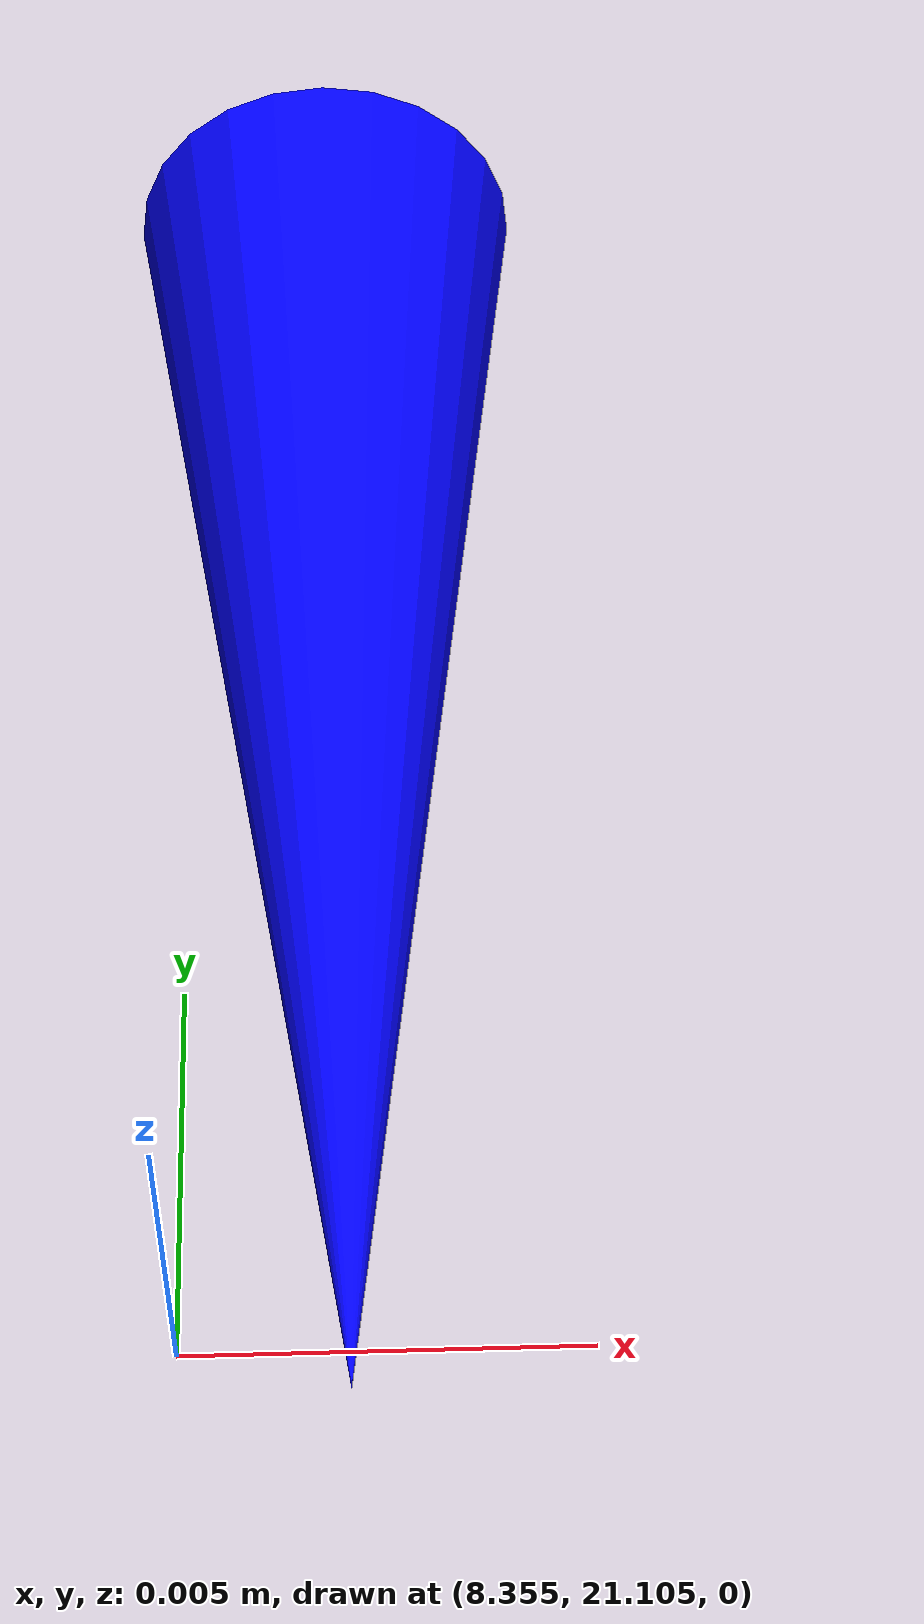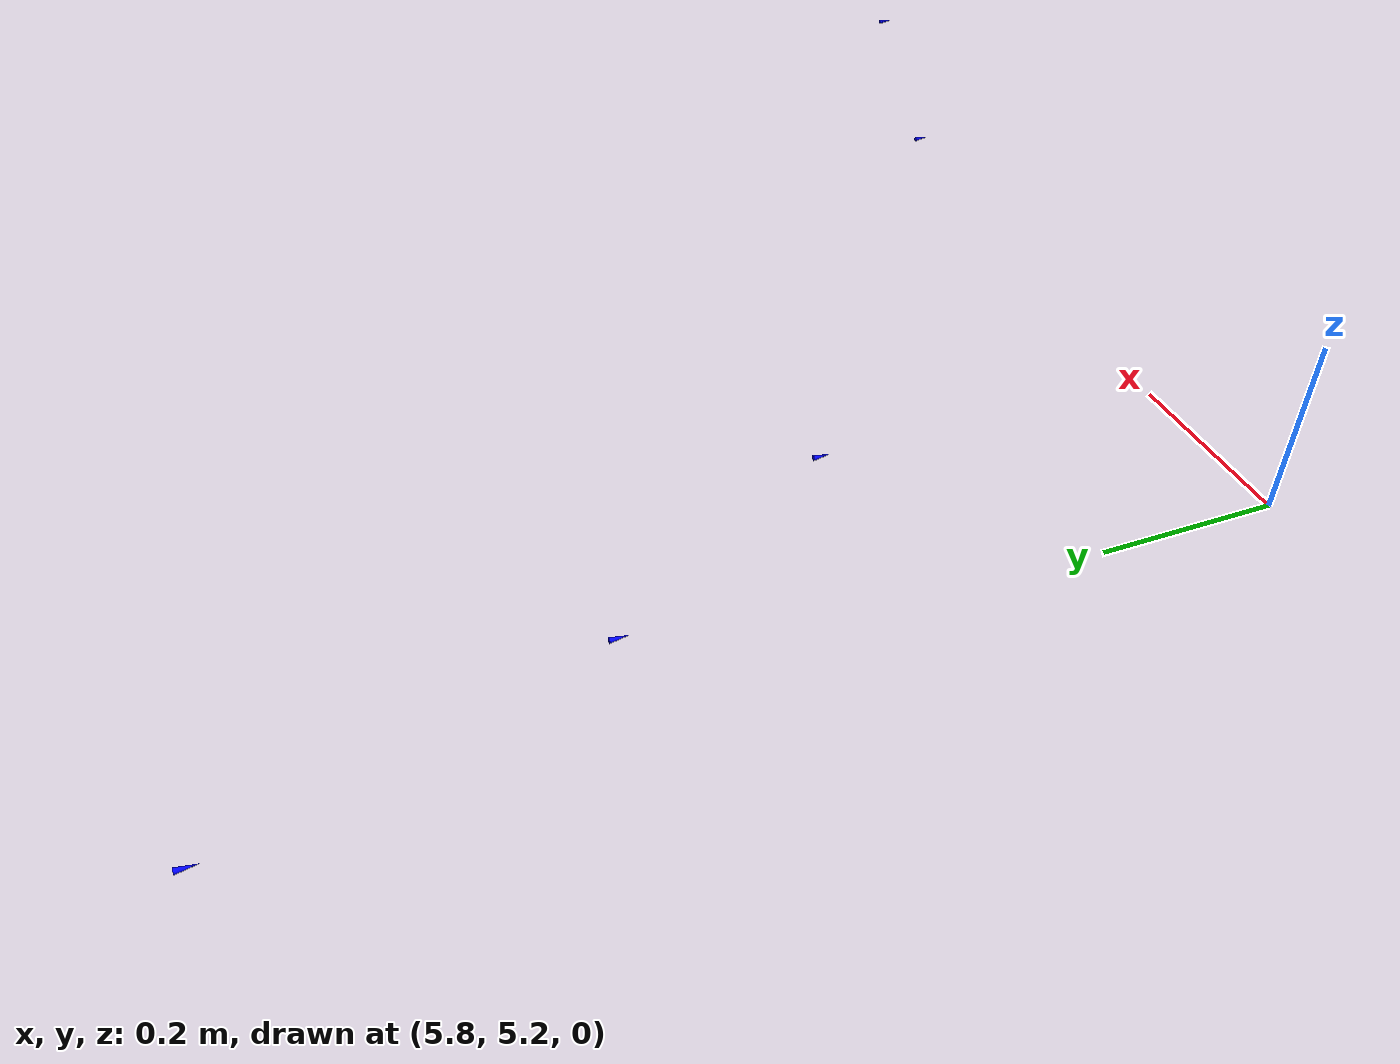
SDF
<?xml version="1.0"?>

<sdf version='1.9'>
<world name='track_blue'>
      <model name='cone_152'>
        <link name='cone_152_link'>
        <inertial>
          <mass>0</mass>
          <inertia>
          <ixx>0.166667</ixx>
          <ixy>0</ixy>
          <ixz>0</ixz>
          <iyy>0.166667</iyy>
          <iyz>0</iyz>
          <izz>0.166667</izz>
          </inertia>
        </inertial>
          <collision name='cone_152_collision'>
            <geometry>
              <mesh>
                <uri>/models/cone/meshes/cone.stl</uri>
                <scale>0.001 0.001 0.001</scale>
              </mesh>
            </geometry>
          </collision>
          <visual name='cone_152_visual'>
            <geometry>
              <mesh>
                <uri>/models/cone/meshes/cone.stl</uri>
                <scale>0.001 0.001 0.001</scale>
              </mesh>
            </geometry>
            <material>
              <ambient>0 0 1 1</ambient>
              <diffuse>0 0 1 1</diffuse>
              <specular>0 0 1 1</specular>
            </material>
          </visual>

          <enable_wind>false</enable_wind>
        </link>
        <pose>5.954227335571712 21.053557327127066 0.0 1.57 0 0</pose>
        <static>true</static>
      </model>

     <model name='cone_153'>
      <link name='cone_153_link'>
        <inertial>
			<mass>0</mass>
			<inertia>
			<ixx>0.166667</ixx>
			<ixy>0</ixy>
			<ixz>0</ixz>
			<iyy>0.166667</iyy>
			<iyz>0</iyz>
			<izz>0.166667</izz>
			</inertia>
		</inertial>
        <collision name='cone_153_collision'>
          <geometry>
            <mesh>
              <uri>/models/cone/meshes/cone.stl</uri>
              <scale>0.001 0.001 0.001</scale>
            </mesh>
          </geometry>
        </collision>
        <visual name='cone_153_visual'>
          <geometry>
            <mesh>
              <uri>/models/cone/meshes/cone.stl</uri>
              <scale>0.001 0.001 0.001</scale>
            </mesh>
          </geometry>
          <material>
            <ambient>0 0 1 1</ambient>
            <diffuse>0 0 1 1</diffuse>
            <specular>0 0 1 1</specular>
          </material>
        </visual>

        <enable_wind>false</enable_wind>
      </link>
      <pose>6.552886556813654 21.073175930411125 0.0 1.57 0 0</pose>
      <static>true</static>
      </model>

     <model name='cone_154'>
      <link name='cone_154_link'>
        <inertial>
			<mass>0</mass>
			<inertia>
			<ixx>0.166667</ixx>
			<ixy>0</ixy>
			<ixz>0</ixz>
			<iyy>0.166667</iyy>
			<iyz>0</iyz>
			<izz>0.166667</izz>
			</inertia>
		</inertial>
        <collision name='cone_154_collision'>
          <geometry>
            <mesh>
              <uri>/models/cone/meshes/cone.stl</uri>
              <scale>0.001 0.001 0.001</scale>
            </mesh>
          </geometry>
        </collision>
        <visual name='cone_154_visual'>
          <geometry>
            <mesh>
              <uri>/models/cone/meshes/cone.stl</uri>
              <scale>0.001 0.001 0.001</scale>
            </mesh>
          </geometry>
          <material>
            <ambient>0 0 1 1</ambient>
            <diffuse>0 0 1 1</diffuse>
            <specular>0 0 1 1</specular>
          </material>
        </visual>

        <enable_wind>false</enable_wind>
      </link>
      <pose>7.152892878518953 21.092141124270682 0.0 1.57 0 0</pose>
      <static>true</static>
      </model>

     <model name='cone_155'>
      <link name='cone_155_link'>
        <inertial>
			<mass>0</mass>
			<inertia>
			<ixx>0.166667</ixx>
			<ixy>0</ixy>
			<ixz>0</ixz>
			<iyy>0.166667</iyy>
			<iyz>0</iyz>
			<izz>0.166667</izz>
			</inertia>
		</inertial>
        <collision name='cone_155_collision'>
          <geometry>
            <mesh>
              <uri>/models/cone/meshes/cone.stl</uri>
              <scale>0.001 0.001 0.001</scale>
            </mesh>
          </geometry>
        </collision>
        <visual name='cone_155_visual'>
          <geometry>
            <mesh>
              <uri>/models/cone/meshes/cone.stl</uri>
              <scale>0.001 0.001 0.001</scale>
            </mesh>
          </geometry>
          <material>
            <ambient>0 0 1 1</ambient>
            <diffuse>0 0 1 1</diffuse>
            <specular>0 0 1 1</specular>
          </material>
        </visual>

        <enable_wind>false</enable_wind>
      </link>
      <pose>7.754271791342774 21.109564147447763 0.0 1.57 0 0</pose>
      <static>true</static>
      </model>

     <model name='cone_156'>
      <link name='cone_156_link'>
        <inertial>
			<mass>0</mass>
			<inertia>
			<ixx>0.166667</ixx>
			<ixy>0</ixy>
			<ixz>0</ixz>
			<iyy>0.166667</iyy>
			<iyz>0</iyz>
			<izz>0.166667</izz>
			</inertia>
		</inertial>
        <collision name='cone_156_collision'>
          <geometry>
            <mesh>
              <uri>/models/cone/meshes/cone.stl</uri>
              <scale>0.001 0.001 0.001</scale>
            </mesh>
          </geometry>
        </collision>
        <visual name='cone_156_visual'>
          <geometry>
            <mesh>
              <uri>/models/cone/meshes/cone.stl</uri>
              <scale>0.001 0.001 0.001</scale>
            </mesh>
          </geometry>
          <material>
            <ambient>0 0 1 1</ambient>
            <diffuse>0 0 1 1</diffuse>
            <specular>0 0 1 1</specular>
          </material>
        </visual>

        <enable_wind>false</enable_wind>
      </link>
      <pose>8.357041939194703 21.124550190319855 0.0 1.57 0 0</pose>
      <static>true</static>
      </model>

     <model name='cone_157'>
      <link name='cone_157_link'>
        <inertial>
			<mass>0</mass>
			<inertia>
			<ixx>0.166667</ixx>
			<ixy>0</ixy>
			<ixz>0</ixz>
			<iyy>0.166667</iyy>
			<iyz>0</iyz>
			<izz>0.166667</izz>
			</inertia>
		</inertial>
        <collision name='cone_157_collision'>
          <geometry>
            <mesh>
              <uri>/models/cone/meshes/cone.stl</uri>
              <scale>0.001 0.001 0.001</scale>
            </mesh>
          </geometry>
        </collision>
        <visual name='cone_157_visual'>
          <geometry>
            <mesh>
              <uri>/models/cone/meshes/cone.stl</uri>
              <scale>0.001 0.001 0.001</scale>
            </mesh>
          </geometry>
          <material>
            <ambient>0 0 1 1</ambient>
            <diffuse>0 0 1 1</diffuse>
            <specular>0 0 1 1</specular>
          </material>
        </visual>

        <enable_wind>false</enable_wind>
      </link>
      <pose>8.961211125505724 21.136198345748667 0.0 1.57 0 0</pose>
      <static>true</static>
      </model>

     <model name='cone_158'>
      <link name='cone_158_link'>
        <inertial>
			<mass>0</mass>
			<inertia>
			<ixx>0.166667</ixx>
			<ixy>0</ixy>
			<ixz>0</ixz>
			<iyy>0.166667</iyy>
			<iyz>0</iyz>
			<izz>0.166667</izz>
			</inertia>
		</inertial>
        <collision name='cone_158_collision'>
          <geometry>
            <mesh>
              <uri>/models/cone/meshes/cone.stl</uri>
              <scale>0.001 0.001 0.001</scale>
            </mesh>
          </geometry>
        </collision>
        <visual name='cone_158_visual'>
          <geometry>
            <mesh>
              <uri>/models/cone/meshes/cone.stl</uri>
              <scale>0.001 0.001 0.001</scale>
            </mesh>
          </geometry>
          <material>
            <ambient>0 0 1 1</ambient>
            <diffuse>0 0 1 1</diffuse>
            <specular>0 0 1 1</specular>
          </material>
        </visual>

        <enable_wind>false</enable_wind>
      </link>
      <pose>10.781943235087184 21.142016413614925 0.0 1.57 0 0</pose>
      <static>true</static>
      </model>

     <model name='cone_159'>
      <link name='cone_159_link'>
        <inertial>
			<mass>0</mass>
			<inertia>
			<ixx>0.166667</ixx>
			<ixy>0</ixy>
			<ixz>0</ixz>
			<iyy>0.166667</iyy>
			<iyz>0</iyz>
			<izz>0.166667</izz>
			</inertia>
		</inertial>
        <collision name='cone_159_collision'>
          <geometry>
            <mesh>
              <uri>/models/cone/meshes/cone.stl</uri>
              <scale>0.001 0.001 0.001</scale>
            </mesh>
          </geometry>
        </collision>
        <visual name='cone_159_visual'>
          <geometry>
            <mesh>
              <uri>/models/cone/meshes/cone.stl</uri>
              <scale>0.001 0.001 0.001</scale>
            </mesh>
          </geometry>
          <material>
            <ambient>0 0 1 1</ambient>
            <diffuse>0 0 1 1</diffuse>
            <specular>0 0 1 1</specular>
          </material>
        </visual>

        <enable_wind>false</enable_wind>
      </link>
      <pose>11.391427557664635 21.131185626865616 0.0 1.57 0 0</pose>
      <static>true</static>
      </model>

     <model name='cone_160'>
      <link name='cone_160_link'>
        <inertial>
			<mass>0</mass>
			<inertia>
			<ixx>0.166667</ixx>
			<ixy>0</ixy>
			<ixz>0</ixz>
			<iyy>0.166667</iyy>
			<iyz>0</iyz>
			<izz>0.166667</izz>
			</inertia>
		</inertial>
        <collision name='cone_160_collision'>
          <geometry>
            <mesh>
              <uri>/models/cone/meshes/cone.stl</uri>
              <scale>0.001 0.001 0.001</scale>
            </mesh>
          </geometry>
        </collision>
        <visual name='cone_160_visual'>
          <geometry>
            <mesh>
              <uri>/models/cone/meshes/cone.stl</uri>
              <scale>0.001 0.001 0.001</scale>
            </mesh>
          </geometry>
          <material>
            <ambient>0 0 1 1</ambient>
            <diffuse>0 0 1 1</diffuse>
            <specular>0 0 1 1</specular>
          </material>
        </visual>

        <enable_wind>false</enable_wind>
      </link>
      <pose>12.002044509248803 21.112426561985757 0.0 1.57 0 0</pose>
      <static>true</static>
      </model>

     <model name='cone_161'>
      <link name='cone_161_link'>
        <inertial>
			<mass>0</mass>
			<inertia>
			<ixx>0.166667</ixx>
			<ixy>0</ixy>
			<ixz>0</ixz>
			<iyy>0.166667</iyy>
			<iyz>0</iyz>
			<izz>0.166667</izz>
			</inertia>
		</inertial>
        <collision name='cone_161_collision'>
          <geometry>
            <mesh>
              <uri>/models/cone/meshes/cone.stl</uri>
              <scale>0.001 0.001 0.001</scale>
            </mesh>
          </geometry>
        </collision>
        <visual name='cone_161_visual'>
          <geometry>
            <mesh>
              <uri>/models/cone/meshes/cone.stl</uri>
              <scale>0.001 0.001 0.001</scale>
            </mesh>
          </geometry>
          <material>
            <ambient>0 0 1 1</ambient>
            <diffuse>0 0 1 1</diffuse>
            <specular>0 0 1 1</specular>
          </material>
        </visual>

        <enable_wind>false</enable_wind>
      </link>
      <pose>12.613650615098113 21.084807331042136 0.0 1.57 0 0</pose>
      <static>true</static>
      </model>

     <model name='cone_162'>
      <link name='cone_162_link'>
        <inertial>
			<mass>0</mass>
			<inertia>
			<ixx>0.166667</ixx>
			<ixy>0</ixy>
			<ixz>0</ixz>
			<iyy>0.166667</iyy>
			<iyz>0</iyz>
			<izz>0.166667</izz>
			</inertia>
		</inertial>
        <collision name='cone_162_collision'>
          <geometry>
            <mesh>
              <uri>/models/cone/meshes/cone.stl</uri>
              <scale>0.001 0.001 0.001</scale>
            </mesh>
          </geometry>
        </collision>
        <visual name='cone_162_visual'>
          <geometry>
            <mesh>
              <uri>/models/cone/meshes/cone.stl</uri>
              <scale>0.001 0.001 0.001</scale>
            </mesh>
          </geometry>
          <material>
            <ambient>0 0 1 1</ambient>
            <diffuse>0 0 1 1</diffuse>
            <specular>0 0 1 1</specular>
          </material>
        </visual>

        <enable_wind>false</enable_wind>
      </link>
      <pose>13.237241676777494 21.044226560695975 0.0 1.57 0 0</pose>
      <static>true</static>
      </model>

     <model name='cone_163'>
      <link name='cone_163_link'>
        <inertial>
			<mass>0</mass>
			<inertia>
			<ixx>0.166667</ixx>
			<ixy>0</ixy>
			<ixz>0</ixz>
			<iyy>0.166667</iyy>
			<iyz>0</iyz>
			<izz>0.166667</izz>
			</inertia>
		</inertial>
        <collision name='cone_163_collision'>
          <geometry>
            <mesh>
              <uri>/models/cone/meshes/cone.stl</uri>
              <scale>0.001 0.001 0.001</scale>
            </mesh>
          </geometry>
        </collision>
        <visual name='cone_163_visual'>
          <geometry>
            <mesh>
              <uri>/models/cone/meshes/cone.stl</uri>
              <scale>0.001 0.001 0.001</scale>
            </mesh>
          </geometry>
          <material>
            <ambient>0 0 1 1</ambient>
            <diffuse>0 0 1 1</diffuse>
            <specular>0 0 1 1</specular>
          </material>
        </visual>

        <enable_wind>false</enable_wind>
      </link>
      <pose>13.886407890761713 20.972516040803814 0.0 1.57 0 0</pose>
      <static>true</static>
      </model>

     <model name='cone_164'>
      <link name='cone_164_link'>
        <inertial>
			<mass>0</mass>
			<inertia>
			<ixx>0.166667</ixx>
			<ixy>0</ixy>
			<ixz>0</ixz>
			<iyy>0.166667</iyy>
			<iyz>0</iyz>
			<izz>0.166667</izz>
			</inertia>
		</inertial>
        <collision name='cone_164_collision'>
          <geometry>
            <mesh>
              <uri>/models/cone/meshes/cone.stl</uri>
              <scale>0.001 0.001 0.001</scale>
            </mesh>
          </geometry>
        </collision>
        <visual name='cone_164_visual'>
          <geometry>
            <mesh>
              <uri>/models/cone/meshes/cone.stl</uri>
              <scale>0.001 0.001 0.001</scale>
            </mesh>
          </geometry>
          <material>
            <ambient>0 0 1 1</ambient>
            <diffuse>0 0 1 1</diffuse>
            <specular>0 0 1 1</specular>
          </material>
        </visual>

        <enable_wind>false</enable_wind>
      </link>
      <pose>14.555933880300042 20.846132572578025 0.0 1.57 0 0</pose>
      <static>true</static>
      </model>

     <model name='cone_165'>
      <link name='cone_165_link'>
        <inertial>
			<mass>0</mass>
			<inertia>
			<ixx>0.166667</ixx>
			<ixy>0</ixy>
			<ixz>0</ixz>
			<iyy>0.166667</iyy>
			<iyz>0</iyz>
			<izz>0.166667</izz>
			</inertia>
		</inertial>
        <collision name='cone_165_collision'>
          <geometry>
            <mesh>
              <uri>/models/cone/meshes/cone.stl</uri>
              <scale>0.001 0.001 0.001</scale>
            </mesh>
          </geometry>
        </collision>
        <visual name='cone_165_visual'>
          <geometry>
            <mesh>
              <uri>/models/cone/meshes/cone.stl</uri>
              <scale>0.001 0.001 0.001</scale>
            </mesh>
          </geometry>
          <material>
            <ambient>0 0 1 1</ambient>
            <diffuse>0 0 1 1</diffuse>
            <specular>0 0 1 1</specular>
          </material>
        </visual>

        <enable_wind>false</enable_wind>
      </link>
      <pose>15.904019802936883 20.329768713294715 0.0 1.57 0 0</pose>
      <static>true</static>
      </model>

     <model name='cone_166'>
      <link name='cone_166_link'>
        <inertial>
			<mass>0</mass>
			<inertia>
			<ixx>0.166667</ixx>
			<ixy>0</ixy>
			<ixz>0</ixz>
			<iyy>0.166667</iyy>
			<iyz>0</iyz>
			<izz>0.166667</izz>
			</inertia>
		</inertial>
        <collision name='cone_166_collision'>
          <geometry>
            <mesh>
              <uri>/models/cone/meshes/cone.stl</uri>
              <scale>0.001 0.001 0.001</scale>
            </mesh>
          </geometry>
        </collision>
        <visual name='cone_166_visual'>
          <geometry>
            <mesh>
              <uri>/models/cone/meshes/cone.stl</uri>
              <scale>0.001 0.001 0.001</scale>
            </mesh>
          </geometry>
          <material>
            <ambient>0 0 1 1</ambient>
            <diffuse>0 0 1 1</diffuse>
            <specular>0 0 1 1</specular>
          </material>
        </visual>

        <enable_wind>false</enable_wind>
      </link>
      <pose>16.5303623144563 19.897405198089924 0.0 1.57 0 0</pose>
      <static>true</static>
      </model>

     <model name='cone_167'>
      <link name='cone_167_link'>
        <inertial>
			<mass>0</mass>
			<inertia>
			<ixx>0.166667</ixx>
			<ixy>0</ixy>
			<ixz>0</ixz>
			<iyy>0.166667</iyy>
			<iyz>0</iyz>
			<izz>0.166667</izz>
			</inertia>
		</inertial>
        <collision name='cone_167_collision'>
          <geometry>
            <mesh>
              <uri>/models/cone/meshes/cone.stl</uri>
              <scale>0.001 0.001 0.001</scale>
            </mesh>
          </geometry>
        </collision>
        <visual name='cone_167_visual'>
          <geometry>
            <mesh>
              <uri>/models/cone/meshes/cone.stl</uri>
              <scale>0.001 0.001 0.001</scale>
            </mesh>
          </geometry>
          <material>
            <ambient>0 0 1 1</ambient>
            <diffuse>0 0 1 1</diffuse>
            <specular>0 0 1 1</specular>
          </material>
        </visual>

        <enable_wind>false</enable_wind>
      </link>
      <pose>17.494910362714872 18.768566105565718 0.0 1.57 0 0</pose>
      <static>true</static>
      </model>

     <model name='cone_168'>
      <link name='cone_168_link'>
        <inertial>
			<mass>0</mass>
			<inertia>
			<ixx>0.166667</ixx>
			<ixy>0</ixy>
			<ixz>0</ixz>
			<iyy>0.166667</iyy>
			<iyz>0</iyz>
			<izz>0.166667</izz>
			</inertia>
		</inertial>
        <collision name='cone_168_collision'>
          <geometry>
            <mesh>
              <uri>/models/cone/meshes/cone.stl</uri>
              <scale>0.001 0.001 0.001</scale>
            </mesh>
          </geometry>
        </collision>
        <visual name='cone_168_visual'>
          <geometry>
            <mesh>
              <uri>/models/cone/meshes/cone.stl</uri>
              <scale>0.001 0.001 0.001</scale>
            </mesh>
          </geometry>
          <material>
            <ambient>0 0 1 1</ambient>
            <diffuse>0 0 1 1</diffuse>
            <specular>0 0 1 1</specular>
          </material>
        </visual>

        <enable_wind>false</enable_wind>
      </link>
      <pose>17.82712958958211 18.127167073594194 0.0 1.57 0 0</pose>
      <static>true</static>
      </model>

     <model name='cone_169'>
      <link name='cone_169_link'>
        <inertial>
			<mass>0</mass>
			<inertia>
			<ixx>0.166667</ixx>
			<ixy>0</ixy>
			<ixz>0</ixz>
			<iyy>0.166667</iyy>
			<iyz>0</iyz>
			<izz>0.166667</izz>
			</inertia>
		</inertial>
        <collision name='cone_169_collision'>
          <geometry>
            <mesh>
              <uri>/models/cone/meshes/cone.stl</uri>
              <scale>0.001 0.001 0.001</scale>
            </mesh>
          </geometry>
        </collision>
        <visual name='cone_169_visual'>
          <geometry>
            <mesh>
              <uri>/models/cone/meshes/cone.stl</uri>
              <scale>0.001 0.001 0.001</scale>
            </mesh>
          </geometry>
          <material>
            <ambient>0 0 1 1</ambient>
            <diffuse>0 0 1 1</diffuse>
            <specular>0 0 1 1</specular>
          </material>
        </visual>

        <enable_wind>false</enable_wind>
      </link>
      <pose>18.068548071071053 17.462024379944033 0.0 1.57 0 0</pose>
      <static>true</static>
      </model>

     <model name='cone_170'>
      <link name='cone_170_link'>
        <inertial>
			<mass>0</mass>
			<inertia>
			<ixx>0.166667</ixx>
			<ixy>0</ixy>
			<ixz>0</ixz>
			<iyy>0.166667</iyy>
			<iyz>0</iyz>
			<izz>0.166667</izz>
			</inertia>
		</inertial>
        <collision name='cone_170_collision'>
          <geometry>
            <mesh>
              <uri>/models/cone/meshes/cone.stl</uri>
              <scale>0.001 0.001 0.001</scale>
            </mesh>
          </geometry>
        </collision>
        <visual name='cone_170_visual'>
          <geometry>
            <mesh>
              <uri>/models/cone/meshes/cone.stl</uri>
              <scale>0.001 0.001 0.001</scale>
            </mesh>
          </geometry>
          <material>
            <ambient>0 0 1 1</ambient>
            <diffuse>0 0 1 1</diffuse>
            <specular>0 0 1 1</specular>
          </material>
        </visual>

        <enable_wind>false</enable_wind>
      </link>
      <pose>18.22865018847571 16.772658685554838 0.0 1.57 0 0</pose>
      <static>true</static>
      </model>

     <model name='cone_171'>
      <link name='cone_171_link'>
        <inertial>
			<mass>0</mass>
			<inertia>
			<ixx>0.166667</ixx>
			<ixy>0</ixy>
			<ixz>0</ixz>
			<iyy>0.166667</iyy>
			<iyz>0</iyz>
			<izz>0.166667</izz>
			</inertia>
		</inertial>
        <collision name='cone_171_collision'>
          <geometry>
            <mesh>
              <uri>/models/cone/meshes/cone.stl</uri>
              <scale>0.001 0.001 0.001</scale>
            </mesh>
          </geometry>
        </collision>
        <visual name='cone_171_visual'>
          <geometry>
            <mesh>
              <uri>/models/cone/meshes/cone.stl</uri>
              <scale>0.001 0.001 0.001</scale>
            </mesh>
          </geometry>
          <material>
            <ambient>0 0 1 1</ambient>
            <diffuse>0 0 1 1</diffuse>
            <specular>0 0 1 1</specular>
          </material>
        </visual>

        <enable_wind>false</enable_wind>
      </link>
      <pose>18.277314465342222 15.337092055525435 0.0 1.57 0 0</pose>
      <static>true</static>
      </model>

     <model name='cone_172'>
      <link name='cone_172_link'>
        <inertial>
			<mass>0</mass>
			<inertia>
			<ixx>0.166667</ixx>
			<ixy>0</ixy>
			<ixz>0</ixz>
			<iyy>0.166667</iyy>
			<iyz>0</iyz>
			<izz>0.166667</izz>
			</inertia>
		</inertial>
        <collision name='cone_172_collision'>
          <geometry>
            <mesh>
              <uri>/models/cone/meshes/cone.stl</uri>
              <scale>0.001 0.001 0.001</scale>
            </mesh>
          </geometry>
        </collision>
        <visual name='cone_172_visual'>
          <geometry>
            <mesh>
              <uri>/models/cone/meshes/cone.stl</uri>
              <scale>0.001 0.001 0.001</scale>
            </mesh>
          </geometry>
          <material>
            <ambient>0 0 1 1</ambient>
            <diffuse>0 0 1 1</diffuse>
            <specular>0 0 1 1</specular>
          </material>
        </visual>

        <enable_wind>false</enable_wind>
      </link>
      <pose>18.147853111189544 14.616672197043115 0.0 1.57 0 0</pose>
      <static>true</static>
      </model>

     <model name='cone_173'>
      <link name='cone_173_link'>
        <inertial>
			<mass>0</mass>
			<inertia>
			<ixx>0.166667</ixx>
			<ixy>0</ixy>
			<ixz>0</ixz>
			<iyy>0.166667</iyy>
			<iyz>0</iyz>
			<izz>0.166667</izz>
			</inertia>
		</inertial>
        <collision name='cone_173_collision'>
          <geometry>
            <mesh>
              <uri>/models/cone/meshes/cone.stl</uri>
              <scale>0.001 0.001 0.001</scale>
            </mesh>
          </geometry>
        </collision>
        <visual name='cone_173_visual'>
          <geometry>
            <mesh>
              <uri>/models/cone/meshes/cone.stl</uri>
              <scale>0.001 0.001 0.001</scale>
            </mesh>
          </geometry>
          <material>
            <ambient>0 0 1 1</ambient>
            <diffuse>0 0 1 1</diffuse>
            <specular>0 0 1 1</specular>
          </material>
        </visual>

        <enable_wind>false</enable_wind>
      </link>
      <pose>17.907157728032892 13.916880910088725 0.0 1.57 0 0</pose>
      <static>true</static>
      </model>

     <model name='cone_174'>
      <link name='cone_174_link'>
        <inertial>
			<mass>0</mass>
			<inertia>
			<ixx>0.166667</ixx>
			<ixy>0</ixy>
			<ixz>0</ixz>
			<iyy>0.166667</iyy>
			<iyz>0</iyz>
			<izz>0.166667</izz>
			</inertia>
		</inertial>
        <collision name='cone_174_collision'>
          <geometry>
            <mesh>
              <uri>/models/cone/meshes/cone.stl</uri>
              <scale>0.001 0.001 0.001</scale>
            </mesh>
          </geometry>
        </collision>
        <visual name='cone_174_visual'>
          <geometry>
            <mesh>
              <uri>/models/cone/meshes/cone.stl</uri>
              <scale>0.001 0.001 0.001</scale>
            </mesh>
          </geometry>
          <material>
            <ambient>0 0 1 1</ambient>
            <diffuse>0 0 1 1</diffuse>
            <specular>0 0 1 1</specular>
          </material>
        </visual>

        <enable_wind>false</enable_wind>
      </link>
      <pose>17.557340269377402 13.263359771558665 0.0 1.57 0 0</pose>
      <static>true</static>
      </model>

     <model name='cone_175'>
      <link name='cone_175_link'>
        <inertial>
			<mass>0</mass>
			<inertia>
			<ixx>0.166667</ixx>
			<ixy>0</ixy>
			<ixz>0</ixz>
			<iyy>0.166667</iyy>
			<iyz>0</iyz>
			<izz>0.166667</izz>
			</inertia>
		</inertial>
        <collision name='cone_175_collision'>
          <geometry>
            <mesh>
              <uri>/models/cone/meshes/cone.stl</uri>
              <scale>0.001 0.001 0.001</scale>
            </mesh>
          </geometry>
        </collision>
        <visual name='cone_175_visual'>
          <geometry>
            <mesh>
              <uri>/models/cone/meshes/cone.stl</uri>
              <scale>0.001 0.001 0.001</scale>
            </mesh>
          </geometry>
          <material>
            <ambient>0 0 1 1</ambient>
            <diffuse>0 0 1 1</diffuse>
            <specular>0 0 1 1</specular>
          </material>
        </visual>

        <enable_wind>false</enable_wind>
      </link>
      <pose>17.121294530305693 12.681531179664116 0.0 1.57 0 0</pose>
      <static>true</static>
      </model>

     <model name='cone_176'>
      <link name='cone_176_link'>
        <inertial>
			<mass>0</mass>
			<inertia>
			<ixx>0.166667</ixx>
			<ixy>0</ixy>
			<ixz>0</ixz>
			<iyy>0.166667</iyy>
			<iyz>0</iyz>
			<izz>0.166667</izz>
			</inertia>
		</inertial>
        <collision name='cone_176_collision'>
          <geometry>
            <mesh>
              <uri>/models/cone/meshes/cone.stl</uri>
              <scale>0.001 0.001 0.001</scale>
            </mesh>
          </geometry>
        </collision>
        <visual name='cone_176_visual'>
          <geometry>
            <mesh>
              <uri>/models/cone/meshes/cone.stl</uri>
              <scale>0.001 0.001 0.001</scale>
            </mesh>
          </geometry>
          <material>
            <ambient>0 0 1 1</ambient>
            <diffuse>0 0 1 1</diffuse>
            <specular>0 0 1 1</specular>
          </material>
        </visual>

        <enable_wind>false</enable_wind>
      </link>
      <pose>16.076112952754023 11.739060455403084 0.0 1.57 0 0</pose>
      <static>true</static>
      </model>

     <model name='cone_177'>
      <link name='cone_177_link'>
        <inertial>
			<mass>0</mass>
			<inertia>
			<ixx>0.166667</ixx>
			<ixy>0</ixy>
			<ixz>0</ixz>
			<iyy>0.166667</iyy>
			<iyz>0</iyz>
			<izz>0.166667</izz>
			</inertia>
		</inertial>
        <collision name='cone_177_collision'>
          <geometry>
            <mesh>
              <uri>/models/cone/meshes/cone.stl</uri>
              <scale>0.001 0.001 0.001</scale>
            </mesh>
          </geometry>
        </collision>
        <visual name='cone_177_visual'>
          <geometry>
            <mesh>
              <uri>/models/cone/meshes/cone.stl</uri>
              <scale>0.001 0.001 0.001</scale>
            </mesh>
          </geometry>
          <material>
            <ambient>0 0 1 1</ambient>
            <diffuse>0 0 1 1</diffuse>
            <specular>0 0 1 1</specular>
          </material>
        </visual>

        <enable_wind>false</enable_wind>
      </link>
      <pose>14.866505101671883 11.056732913881735 0.0 1.57 0 0</pose>
      <static>true</static>
      </model>

     <model name='cone_178'>
      <link name='cone_178_link'>
        <inertial>
			<mass>0</mass>
			<inertia>
			<ixx>0.166667</ixx>
			<ixy>0</ixy>
			<ixz>0</ixz>
			<iyy>0.166667</iyy>
			<iyz>0</iyz>
			<izz>0.166667</izz>
			</inertia>
		</inertial>
        <collision name='cone_178_collision'>
          <geometry>
            <mesh>
              <uri>/models/cone/meshes/cone.stl</uri>
              <scale>0.001 0.001 0.001</scale>
            </mesh>
          </geometry>
        </collision>
        <visual name='cone_178_visual'>
          <geometry>
            <mesh>
              <uri>/models/cone/meshes/cone.stl</uri>
              <scale>0.001 0.001 0.001</scale>
            </mesh>
          </geometry>
          <material>
            <ambient>0 0 1 1</ambient>
            <diffuse>0 0 1 1</diffuse>
            <specular>0 0 1 1</specular>
          </material>
        </visual>

        <enable_wind>false</enable_wind>
      </link>
      <pose>14.205014846682733 10.818204662053315 0.0 1.57 0 0</pose>
      <static>true</static>
      </model>

     <model name='cone_179'>
      <link name='cone_179_link'>
        <inertial>
			<mass>0</mass>
			<inertia>
			<ixx>0.166667</ixx>
			<ixy>0</ixy>
			<ixz>0</ixz>
			<iyy>0.166667</iyy>
			<iyz>0</iyz>
			<izz>0.166667</izz>
			</inertia>
		</inertial>
        <collision name='cone_179_collision'>
          <geometry>
            <mesh>
              <uri>/models/cone/meshes/cone.stl</uri>
              <scale>0.001 0.001 0.001</scale>
            </mesh>
          </geometry>
        </collision>
        <visual name='cone_179_visual'>
          <geometry>
            <mesh>
              <uri>/models/cone/meshes/cone.stl</uri>
              <scale>0.001 0.001 0.001</scale>
            </mesh>
          </geometry>
          <material>
            <ambient>0 0 1 1</ambient>
            <diffuse>0 0 1 1</diffuse>
            <specular>0 0 1 1</specular>
          </material>
        </visual>

        <enable_wind>false</enable_wind>
      </link>
      <pose>13.514748179388253 10.659110453971975 0.0 1.57 0 0</pose>
      <static>true</static>
      </model>

     <model name='cone_180'>
      <link name='cone_180_link'>
        <inertial>
			<mass>0</mass>
			<inertia>
			<ixx>0.166667</ixx>
			<ixy>0</ixy>
			<ixz>0</ixz>
			<iyy>0.166667</iyy>
			<iyz>0</iyz>
			<izz>0.166667</izz>
			</inertia>
		</inertial>
        <collision name='cone_180_collision'>
          <geometry>
            <mesh>
              <uri>/models/cone/meshes/cone.stl</uri>
              <scale>0.001 0.001 0.001</scale>
            </mesh>
          </geometry>
        </collision>
        <visual name='cone_180_visual'>
          <geometry>
            <mesh>
              <uri>/models/cone/meshes/cone.stl</uri>
              <scale>0.001 0.001 0.001</scale>
            </mesh>
          </geometry>
          <material>
            <ambient>0 0 1 1</ambient>
            <diffuse>0 0 1 1</diffuse>
            <specular>0 0 1 1</specular>
          </material>
        </visual>

        <enable_wind>false</enable_wind>
      </link>
      <pose>12.804853979535283 10.587046639760876 0.0 1.57 0 0</pose>
      <static>true</static>
      </model>

     <model name='cone_181'>
      <link name='cone_181_link'>
        <inertial>
			<mass>0</mass>
			<inertia>
			<ixx>0.166667</ixx>
			<ixy>0</ixy>
			<ixz>0</ixz>
			<iyy>0.166667</iyy>
			<iyz>0</iyz>
			<izz>0.166667</izz>
			</inertia>
		</inertial>
        <collision name='cone_181_collision'>
          <geometry>
            <mesh>
              <uri>/models/cone/meshes/cone.stl</uri>
              <scale>0.001 0.001 0.001</scale>
            </mesh>
          </geometry>
        </collision>
        <visual name='cone_181_visual'>
          <geometry>
            <mesh>
              <uri>/models/cone/meshes/cone.stl</uri>
              <scale>0.001 0.001 0.001</scale>
            </mesh>
          </geometry>
          <material>
            <ambient>0 0 1 1</ambient>
            <diffuse>0 0 1 1</diffuse>
            <specular>0 0 1 1</specular>
          </material>
        </visual>

        <enable_wind>false</enable_wind>
      </link>
      <pose>12.090639431864414 10.607506089269306 0.0 1.57 0 0</pose>
      <static>true</static>
      </model>

     <model name='cone_182'>
      <link name='cone_182_link'>
        <inertial>
			<mass>0</mass>
			<inertia>
			<ixx>0.166667</ixx>
			<ixy>0</ixy>
			<ixz>0</ixz>
			<iyy>0.166667</iyy>
			<iyz>0</iyz>
			<izz>0.166667</izz>
			</inertia>
		</inertial>
        <collision name='cone_182_collision'>
          <geometry>
            <mesh>
              <uri>/models/cone/meshes/cone.stl</uri>
              <scale>0.001 0.001 0.001</scale>
            </mesh>
          </geometry>
        </collision>
        <visual name='cone_182_visual'>
          <geometry>
            <mesh>
              <uri>/models/cone/meshes/cone.stl</uri>
              <scale>0.001 0.001 0.001</scale>
            </mesh>
          </geometry>
          <material>
            <ambient>0 0 1 1</ambient>
            <diffuse>0 0 1 1</diffuse>
            <specular>0 0 1 1</specular>
          </material>
        </visual>

        <enable_wind>false</enable_wind>
      </link>
      <pose>11.394051861887743 10.714746248011975 0.0 1.57 0 0</pose>
      <static>true</static>
      </model>

     <model name='cone_183'>
      <link name='cone_183_link'>
        <inertial>
			<mass>0</mass>
			<inertia>
			<ixx>0.166667</ixx>
			<ixy>0</ixy>
			<ixz>0</ixz>
			<iyy>0.166667</iyy>
			<iyz>0</iyz>
			<izz>0.166667</izz>
			</inertia>
		</inertial>
        <collision name='cone_183_collision'>
          <geometry>
            <mesh>
              <uri>/models/cone/meshes/cone.stl</uri>
              <scale>0.001 0.001 0.001</scale>
            </mesh>
          </geometry>
        </collision>
        <visual name='cone_183_visual'>
          <geometry>
            <mesh>
              <uri>/models/cone/meshes/cone.stl</uri>
              <scale>0.001 0.001 0.001</scale>
            </mesh>
          </geometry>
          <material>
            <ambient>0 0 1 1</ambient>
            <diffuse>0 0 1 1</diffuse>
            <specular>0 0 1 1</specular>
          </material>
        </visual>

        <enable_wind>false</enable_wind>
      </link>
      <pose>10.723839480164834 10.896973850123576 0.0 1.57 0 0</pose>
      <static>true</static>
      </model>

     <model name='cone_184'>
      <link name='cone_184_link'>
        <inertial>
			<mass>0</mass>
			<inertia>
			<ixx>0.166667</ixx>
			<ixy>0</ixy>
			<ixz>0</ixz>
			<iyy>0.166667</iyy>
			<iyz>0</iyz>
			<izz>0.166667</izz>
			</inertia>
		</inertial>
        <collision name='cone_184_collision'>
          <geometry>
            <mesh>
              <uri>/models/cone/meshes/cone.stl</uri>
              <scale>0.001 0.001 0.001</scale>
            </mesh>
          </geometry>
        </collision>
        <visual name='cone_184_visual'>
          <geometry>
            <mesh>
              <uri>/models/cone/meshes/cone.stl</uri>
              <scale>0.001 0.001 0.001</scale>
            </mesh>
          </geometry>
          <material>
            <ambient>0 0 1 1</ambient>
            <diffuse>0 0 1 1</diffuse>
            <specular>0 0 1 1</specular>
          </material>
        </visual>

        <enable_wind>false</enable_wind>
      </link>
      <pose>9.480057085583203 11.439439834639614 0.0 1.57 0 0</pose>
      <static>true</static>
      </model>

     <model name='cone_185'>
      <link name='cone_185_link'>
        <inertial>
			<mass>0</mass>
			<inertia>
			<ixx>0.166667</ixx>
			<ixy>0</ixy>
			<ixz>0</ixz>
			<iyy>0.166667</iyy>
			<iyz>0</iyz>
			<izz>0.166667</izz>
			</inertia>
		</inertial>
        <collision name='cone_185_collision'>
          <geometry>
            <mesh>
              <uri>/models/cone/meshes/cone.stl</uri>
              <scale>0.001 0.001 0.001</scale>
            </mesh>
          </geometry>
        </collision>
        <visual name='cone_185_visual'>
          <geometry>
            <mesh>
              <uri>/models/cone/meshes/cone.stl</uri>
              <scale>0.001 0.001 0.001</scale>
            </mesh>
          </geometry>
          <material>
            <ambient>0 0 1 1</ambient>
            <diffuse>0 0 1 1</diffuse>
            <specular>0 0 1 1</specular>
          </material>
        </visual>

        <enable_wind>false</enable_wind>
      </link>
      <pose>8.384333001936223 12.126044624009726 0.0 1.57 0 0</pose>
      <static>true</static>
      </model>

     <model name='cone_186'>
      <link name='cone_186_link'>
        <inertial>
			<mass>0</mass>
			<inertia>
			<ixx>0.166667</ixx>
			<ixy>0</ixy>
			<ixz>0</ixz>
			<iyy>0.166667</iyy>
			<iyz>0</iyz>
			<izz>0.166667</izz>
			</inertia>
		</inertial>
        <collision name='cone_186_collision'>
          <geometry>
            <mesh>
              <uri>/models/cone/meshes/cone.stl</uri>
              <scale>0.001 0.001 0.001</scale>
            </mesh>
          </geometry>
        </collision>
        <visual name='cone_186_visual'>
          <geometry>
            <mesh>
              <uri>/models/cone/meshes/cone.stl</uri>
              <scale>0.001 0.001 0.001</scale>
            </mesh>
          </geometry>
          <material>
            <ambient>0 0 1 1</ambient>
            <diffuse>0 0 1 1</diffuse>
            <specular>0 0 1 1</specular>
          </material>
        </visual>

        <enable_wind>false</enable_wind>
      </link>
      <pose>7.886125315043143 12.476512291449895 0.0 1.57 0 0</pose>
      <static>true</static>
      </model>

     <model name='cone_187'>
      <link name='cone_187_link'>
        <inertial>
			<mass>0</mass>
			<inertia>
			<ixx>0.166667</ixx>
			<ixy>0</ixy>
			<ixz>0</ixz>
			<iyy>0.166667</iyy>
			<iyz>0</iyz>
			<izz>0.166667</izz>
			</inertia>
		</inertial>
        <collision name='cone_187_collision'>
          <geometry>
            <mesh>
              <uri>/models/cone/meshes/cone.stl</uri>
              <scale>0.001 0.001 0.001</scale>
            </mesh>
          </geometry>
        </collision>
        <visual name='cone_187_visual'>
          <geometry>
            <mesh>
              <uri>/models/cone/meshes/cone.stl</uri>
              <scale>0.001 0.001 0.001</scale>
            </mesh>
          </geometry>
          <material>
            <ambient>0 0 1 1</ambient>
            <diffuse>0 0 1 1</diffuse>
            <specular>0 0 1 1</specular>
          </material>
        </visual>

        <enable_wind>false</enable_wind>
      </link>
      <pose>7.407836454265334 12.811374788341556 0.0 1.57 0 0</pose>
      <static>true</static>
      </model>

     <model name='cone_188'>
      <link name='cone_188_link'>
        <inertial>
			<mass>0</mass>
			<inertia>
			<ixx>0.166667</ixx>
			<ixy>0</ixy>
			<ixz>0</ixz>
			<iyy>0.166667</iyy>
			<iyz>0</iyz>
			<izz>0.166667</izz>
			</inertia>
		</inertial>
        <collision name='cone_188_collision'>
          <geometry>
            <mesh>
              <uri>/models/cone/meshes/cone.stl</uri>
              <scale>0.001 0.001 0.001</scale>
            </mesh>
          </geometry>
        </collision>
        <visual name='cone_188_visual'>
          <geometry>
            <mesh>
              <uri>/models/cone/meshes/cone.stl</uri>
              <scale>0.001 0.001 0.001</scale>
            </mesh>
          </geometry>
          <material>
            <ambient>0 0 1 1</ambient>
            <diffuse>0 0 1 1</diffuse>
            <specular>0 0 1 1</specular>
          </material>
        </visual>

        <enable_wind>false</enable_wind>
      </link>
      <pose>6.940783379561563 13.117716989509375 0.0 1.57 0 0</pose>
      <static>true</static>
      </model>

     <model name='cone_189'>
      <link name='cone_189_link'>
        <inertial>
			<mass>0</mass>
			<inertia>
			<ixx>0.166667</ixx>
			<ixy>0</ixy>
			<ixz>0</ixz>
			<iyy>0.166667</iyy>
			<iyz>0</iyz>
			<izz>0.166667</izz>
			</inertia>
		</inertial>
        <collision name='cone_189_collision'>
          <geometry>
            <mesh>
              <uri>/models/cone/meshes/cone.stl</uri>
              <scale>0.001 0.001 0.001</scale>
            </mesh>
          </geometry>
        </collision>
        <visual name='cone_189_visual'>
          <geometry>
            <mesh>
              <uri>/models/cone/meshes/cone.stl</uri>
              <scale>0.001 0.001 0.001</scale>
            </mesh>
          </geometry>
          <material>
            <ambient>0 0 1 1</ambient>
            <diffuse>0 0 1 1</diffuse>
            <specular>0 0 1 1</specular>
          </material>
        </visual>

        <enable_wind>false</enable_wind>
      </link>
      <pose>6.478618244241673 13.383660013804256 0.0 1.57 0 0</pose>
      <static>true</static>
      </model>

     <model name='cone_190'>
      <link name='cone_190_link'>
        <inertial>
			<mass>0</mass>
			<inertia>
			<ixx>0.166667</ixx>
			<ixy>0</ixy>
			<ixz>0</ixz>
			<iyy>0.166667</iyy>
			<iyz>0</iyz>
			<izz>0.166667</izz>
			</inertia>
		</inertial>
        <collision name='cone_190_collision'>
          <geometry>
            <mesh>
              <uri>/models/cone/meshes/cone.stl</uri>
              <scale>0.001 0.001 0.001</scale>
            </mesh>
          </geometry>
        </collision>
        <visual name='cone_190_visual'>
          <geometry>
            <mesh>
              <uri>/models/cone/meshes/cone.stl</uri>
              <scale>0.001 0.001 0.001</scale>
            </mesh>
          </geometry>
          <material>
            <ambient>0 0 1 1</ambient>
            <diffuse>0 0 1 1</diffuse>
            <specular>0 0 1 1</specular>
          </material>
        </visual>

        <enable_wind>false</enable_wind>
      </link>
      <pose>5.535797934038792 13.766441461001996 0.0 1.57 0 0</pose>
      <static>true</static>
      </model>

     <model name='cone_191'>
      <link name='cone_191_link'>
        <inertial>
			<mass>0</mass>
			<inertia>
			<ixx>0.166667</ixx>
			<ixy>0</ixy>
			<ixz>0</ixz>
			<iyy>0.166667</iyy>
			<iyz>0</iyz>
			<izz>0.166667</izz>
			</inertia>
		</inertial>
        <collision name='cone_191_collision'>
          <geometry>
            <mesh>
              <uri>/models/cone/meshes/cone.stl</uri>
              <scale>0.001 0.001 0.001</scale>
            </mesh>
          </geometry>
        </collision>
        <visual name='cone_191_visual'>
          <geometry>
            <mesh>
              <uri>/models/cone/meshes/cone.stl</uri>
              <scale>0.001 0.001 0.001</scale>
            </mesh>
          </geometry>
          <material>
            <ambient>0 0 1 1</ambient>
            <diffuse>0 0 1 1</diffuse>
            <specular>0 0 1 1</specular>
          </material>
        </visual>

        <enable_wind>false</enable_wind>
      </link>
      <pose>5.038708098313799 13.886468167079844 0.0 1.57 0 0</pose>
      <static>true</static>
      </model>

     <model name='cone_192'>
      <link name='cone_192_link'>
        <inertial>
			<mass>0</mass>
			<inertia>
			<ixx>0.166667</ixx>
			<ixy>0</ixy>
			<ixz>0</ixz>
			<iyy>0.166667</iyy>
			<iyz>0</iyz>
			<izz>0.166667</izz>
			</inertia>
		</inertial>
        <collision name='cone_192_collision'>
          <geometry>
            <mesh>
              <uri>/models/cone/meshes/cone.stl</uri>
              <scale>0.001 0.001 0.001</scale>
            </mesh>
          </geometry>
        </collision>
        <visual name='cone_192_visual'>
          <geometry>
            <mesh>
              <uri>/models/cone/meshes/cone.stl</uri>
              <scale>0.001 0.001 0.001</scale>
            </mesh>
          </geometry>
          <material>
            <ambient>0 0 1 1</ambient>
            <diffuse>0 0 1 1</diffuse>
            <specular>0 0 1 1</specular>
          </material>
        </visual>

        <enable_wind>false</enable_wind>
      </link>
      <pose>4.529620224716543 13.959156822505975 0.0 1.57 0 0</pose>
      <static>true</static>
      </model>

     <model name='cone_193'>
      <link name='cone_193_link'>
        <inertial>
			<mass>0</mass>
			<inertia>
			<ixx>0.166667</ixx>
			<ixy>0</ixy>
			<ixz>0</ixz>
			<iyy>0.166667</iyy>
			<iyz>0</iyz>
			<izz>0.166667</izz>
			</inertia>
		</inertial>
        <collision name='cone_193_collision'>
          <geometry>
            <mesh>
              <uri>/models/cone/meshes/cone.stl</uri>
              <scale>0.001 0.001 0.001</scale>
            </mesh>
          </geometry>
        </collision>
        <visual name='cone_193_visual'>
          <geometry>
            <mesh>
              <uri>/models/cone/meshes/cone.stl</uri>
              <scale>0.001 0.001 0.001</scale>
            </mesh>
          </geometry>
          <material>
            <ambient>0 0 1 1</ambient>
            <diffuse>0 0 1 1</diffuse>
            <specular>0 0 1 1</specular>
          </material>
        </visual>

        <enable_wind>false</enable_wind>
      </link>
      <pose>4.0131376363181746 13.984953444918055 0.0 1.57 0 0</pose>
      <static>true</static>
      </model>

     <model name='cone_194'>
      <link name='cone_194_link'>
        <inertial>
			<mass>0</mass>
			<inertia>
			<ixx>0.166667</ixx>
			<ixy>0</ixy>
			<ixz>0</ixz>
			<iyy>0.166667</iyy>
			<iyz>0</iyz>
			<izz>0.166667</izz>
			</inertia>
		</inertial>
        <collision name='cone_194_collision'>
          <geometry>
            <mesh>
              <uri>/models/cone/meshes/cone.stl</uri>
              <scale>0.001 0.001 0.001</scale>
            </mesh>
          </geometry>
        </collision>
        <visual name='cone_194_visual'>
          <geometry>
            <mesh>
              <uri>/models/cone/meshes/cone.stl</uri>
              <scale>0.001 0.001 0.001</scale>
            </mesh>
          </geometry>
          <material>
            <ambient>0 0 1 1</ambient>
            <diffuse>0 0 1 1</diffuse>
            <specular>0 0 1 1</specular>
          </material>
        </visual>

        <enable_wind>false</enable_wind>
      </link>
      <pose>3.0168363064309607 13.896107420098616 0.0 1.57 0 0</pose>
      <static>true</static>
      </model>

     <model name='cone_195'>
      <link name='cone_195_link'>
        <inertial>
			<mass>0</mass>
			<inertia>
			<ixx>0.166667</ixx>
			<ixy>0</ixy>
			<ixz>0</ixz>
			<iyy>0.166667</iyy>
			<iyz>0</iyz>
			<izz>0.166667</izz>
			</inertia>
		</inertial>
        <collision name='cone_195_collision'>
          <geometry>
            <mesh>
              <uri>/models/cone/meshes/cone.stl</uri>
              <scale>0.001 0.001 0.001</scale>
            </mesh>
          </geometry>
        </collision>
        <visual name='cone_195_visual'>
          <geometry>
            <mesh>
              <uri>/models/cone/meshes/cone.stl</uri>
              <scale>0.001 0.001 0.001</scale>
            </mesh>
          </geometry>
          <material>
            <ambient>0 0 1 1</ambient>
            <diffuse>0 0 1 1</diffuse>
            <specular>0 0 1 1</specular>
          </material>
        </visual>

        <enable_wind>false</enable_wind>
      </link>
      <pose>2.5999418083584196 13.769059935278095 0.0 1.57 0 0</pose>
      <static>true</static>
      </model>

     <model name='cone_196'>
      <link name='cone_196_link'>
        <inertial>
			<mass>0</mass>
			<inertia>
			<ixx>0.166667</ixx>
			<ixy>0</ixy>
			<ixz>0</ixz>
			<iyy>0.166667</iyy>
			<iyz>0</iyz>
			<izz>0.166667</izz>
			</inertia>
		</inertial>
        <collision name='cone_196_collision'>
          <geometry>
            <mesh>
              <uri>/models/cone/meshes/cone.stl</uri>
              <scale>0.001 0.001 0.001</scale>
            </mesh>
          </geometry>
        </collision>
        <visual name='cone_196_visual'>
          <geometry>
            <mesh>
              <uri>/models/cone/meshes/cone.stl</uri>
              <scale>0.001 0.001 0.001</scale>
            </mesh>
          </geometry>
          <material>
            <ambient>0 0 1 1</ambient>
            <diffuse>0 0 1 1</diffuse>
            <specular>0 0 1 1</specular>
          </material>
        </visual>

        <enable_wind>false</enable_wind>
      </link>
      <pose>2.0027866524235365 13.338638468344255 0.0 1.57 0 0</pose>
      <static>true</static>
      </model>

     <model name='cone_197'>
      <link name='cone_197_link'>
        <inertial>
			<mass>0</mass>
			<inertia>
			<ixx>0.166667</ixx>
			<ixy>0</ixy>
			<ixz>0</ixz>
			<iyy>0.166667</iyy>
			<iyz>0</iyz>
			<izz>0.166667</izz>
			</inertia>
		</inertial>
        <collision name='cone_197_collision'>
          <geometry>
            <mesh>
              <uri>/models/cone/meshes/cone.stl</uri>
              <scale>0.001 0.001 0.001</scale>
            </mesh>
          </geometry>
        </collision>
        <visual name='cone_197_visual'>
          <geometry>
            <mesh>
              <uri>/models/cone/meshes/cone.stl</uri>
              <scale>0.001 0.001 0.001</scale>
            </mesh>
          </geometry>
          <material>
            <ambient>0 0 1 1</ambient>
            <diffuse>0 0 1 1</diffuse>
            <specular>0 0 1 1</specular>
          </material>
        </visual>

        <enable_wind>false</enable_wind>
      </link>
      <pose>1.8191956238251246 13.033050115553875 0.0 1.57 0 0</pose>
      <static>true</static>
      </model>

     <model name='cone_198'>
      <link name='cone_198_link'>
        <inertial>
			<mass>0</mass>
			<inertia>
			<ixx>0.166667</ixx>
			<ixy>0</ixy>
			<ixz>0</ixz>
			<iyy>0.166667</iyy>
			<iyz>0</iyz>
			<izz>0.166667</izz>
			</inertia>
		</inertial>
        <collision name='cone_198_collision'>
          <geometry>
            <mesh>
              <uri>/models/cone/meshes/cone.stl</uri>
              <scale>0.001 0.001 0.001</scale>
            </mesh>
          </geometry>
        </collision>
        <visual name='cone_198_visual'>
          <geometry>
            <mesh>
              <uri>/models/cone/meshes/cone.stl</uri>
              <scale>0.001 0.001 0.001</scale>
            </mesh>
          </geometry>
          <material>
            <ambient>0 0 1 1</ambient>
            <diffuse>0 0 1 1</diffuse>
            <specular>0 0 1 1</specular>
          </material>
        </visual>

        <enable_wind>false</enable_wind>
      </link>
      <pose>1.7210754775995771 12.685957362659124 0.0 1.57 0 0</pose>
      <static>true</static>
      </model>

     <model name='cone_199'>
      <link name='cone_199_link'>
        <inertial>
			<mass>0</mass>
			<inertia>
			<ixx>0.166667</ixx>
			<ixy>0</ixy>
			<ixz>0</ixz>
			<iyy>0.166667</iyy>
			<iyz>0</iyz>
			<izz>0.166667</izz>
			</inertia>
		</inertial>
        <collision name='cone_199_collision'>
          <geometry>
            <mesh>
              <uri>/models/cone/meshes/cone.stl</uri>
              <scale>0.001 0.001 0.001</scale>
            </mesh>
          </geometry>
        </collision>
        <visual name='cone_199_visual'>
          <geometry>
            <mesh>
              <uri>/models/cone/meshes/cone.stl</uri>
              <scale>0.001 0.001 0.001</scale>
            </mesh>
          </geometry>
          <material>
            <ambient>0 0 1 1</ambient>
            <diffuse>0 0 1 1</diffuse>
            <specular>0 0 1 1</specular>
          </material>
        </visual>

        <enable_wind>false</enable_wind>
      </link>
      <pose>1.7157296904437835 12.321102870727735 0.0 1.57 0 0</pose>
      <static>true</static>
      </model>

     <model name='cone_200'>
      <link name='cone_200_link'>
        <inertial>
			<mass>0</mass>
			<inertia>
			<ixx>0.166667</ixx>
			<ixy>0</ixy>
			<ixz>0</ixz>
			<iyy>0.166667</iyy>
			<iyz>0</iyz>
			<izz>0.166667</izz>
			</inertia>
		</inertial>
        <collision name='cone_200_collision'>
          <geometry>
            <mesh>
              <uri>/models/cone/meshes/cone.stl</uri>
              <scale>0.001 0.001 0.001</scale>
            </mesh>
          </geometry>
        </collision>
        <visual name='cone_200_visual'>
          <geometry>
            <mesh>
              <uri>/models/cone/meshes/cone.stl</uri>
              <scale>0.001 0.001 0.001</scale>
            </mesh>
          </geometry>
          <material>
            <ambient>0 0 1 1</ambient>
            <diffuse>0 0 1 1</diffuse>
            <specular>0 0 1 1</specular>
          </material>
        </visual>

        <enable_wind>false</enable_wind>
      </link>
      <pose>1.8040244521062467 11.962727038273195 0.0 1.57 0 0</pose>
      <static>true</static>
      </model>

     <model name='cone_201'>
      <link name='cone_201_link'>
        <inertial>
			<mass>0</mass>
			<inertia>
			<ixx>0.166667</ixx>
			<ixy>0</ixy>
			<ixz>0</ixz>
			<iyy>0.166667</iyy>
			<iyz>0</iyz>
			<izz>0.166667</izz>
			</inertia>
		</inertial>
        <collision name='cone_201_collision'>
          <geometry>
            <mesh>
              <uri>/models/cone/meshes/cone.stl</uri>
              <scale>0.001 0.001 0.001</scale>
            </mesh>
          </geometry>
        </collision>
        <visual name='cone_201_visual'>
          <geometry>
            <mesh>
              <uri>/models/cone/meshes/cone.stl</uri>
              <scale>0.001 0.001 0.001</scale>
            </mesh>
          </geometry>
          <material>
            <ambient>0 0 1 1</ambient>
            <diffuse>0 0 1 1</diffuse>
            <specular>0 0 1 1</specular>
          </material>
        </visual>

        <enable_wind>false</enable_wind>
      </link>
      <pose>1.9807386704638845 11.633913278643476 0.0 1.57 0 0</pose>
      <static>true</static>
      </model>

     <model name='cone_202'>
      <link name='cone_202_link'>
        <inertial>
			<mass>0</mass>
			<inertia>
			<ixx>0.166667</ixx>
			<ixy>0</ixy>
			<ixz>0</ixz>
			<iyy>0.166667</iyy>
			<iyz>0</iyz>
			<izz>0.166667</izz>
			</inertia>
		</inertial>
        <collision name='cone_202_collision'>
          <geometry>
            <mesh>
              <uri>/models/cone/meshes/cone.stl</uri>
              <scale>0.001 0.001 0.001</scale>
            </mesh>
          </geometry>
        </collision>
        <visual name='cone_202_visual'>
          <geometry>
            <mesh>
              <uri>/models/cone/meshes/cone.stl</uri>
              <scale>0.001 0.001 0.001</scale>
            </mesh>
          </geometry>
          <material>
            <ambient>0 0 1 1</ambient>
            <diffuse>0 0 1 1</diffuse>
            <specular>0 0 1 1</specular>
          </material>
        </visual>

        <enable_wind>false</enable_wind>
      </link>
      <pose>2.2498235202962924 11.336633453011585 0.0 1.57 0 0</pose>
      <static>true</static>
      </model>

     <model name='cone_203'>
      <link name='cone_203_link'>
        <inertial>
			<mass>0</mass>
			<inertia>
			<ixx>0.166667</ixx>
			<ixy>0</ixy>
			<ixz>0</ixz>
			<iyy>0.166667</iyy>
			<iyz>0</iyz>
			<izz>0.166667</izz>
			</inertia>
		</inertial>
        <collision name='cone_203_collision'>
          <geometry>
            <mesh>
              <uri>/models/cone/meshes/cone.stl</uri>
              <scale>0.001 0.001 0.001</scale>
            </mesh>
          </geometry>
        </collision>
        <visual name='cone_203_visual'>
          <geometry>
            <mesh>
              <uri>/models/cone/meshes/cone.stl</uri>
              <scale>0.001 0.001 0.001</scale>
            </mesh>
          </geometry>
          <material>
            <ambient>0 0 1 1</ambient>
            <diffuse>0 0 1 1</diffuse>
            <specular>0 0 1 1</specular>
          </material>
        </visual>

        <enable_wind>false</enable_wind>
      </link>
      <pose>3.6134137273994984 10.448227461812756 0.0 1.57 0 0</pose>
      <static>true</static>
      </model>

     <model name='cone_204'>
      <link name='cone_204_link'>
        <inertial>
			<mass>0</mass>
			<inertia>
			<ixx>0.166667</ixx>
			<ixy>0</ixy>
			<ixz>0</ixz>
			<iyy>0.166667</iyy>
			<iyz>0</iyz>
			<izz>0.166667</izz>
			</inertia>
		</inertial>
        <collision name='cone_204_collision'>
          <geometry>
            <mesh>
              <uri>/models/cone/meshes/cone.stl</uri>
              <scale>0.001 0.001 0.001</scale>
            </mesh>
          </geometry>
        </collision>
        <visual name='cone_204_visual'>
          <geometry>
            <mesh>
              <uri>/models/cone/meshes/cone.stl</uri>
              <scale>0.001 0.001 0.001</scale>
            </mesh>
          </geometry>
          <material>
            <ambient>0 0 1 1</ambient>
            <diffuse>0 0 1 1</diffuse>
            <specular>0 0 1 1</specular>
          </material>
        </visual>

        <enable_wind>false</enable_wind>
      </link>
      <pose>4.181738619630457 10.064779180708946 0.0 1.57 0 0</pose>
      <static>true</static>
      </model>

     <model name='cone_205'>
      <link name='cone_205_link'>
        <inertial>
			<mass>0</mass>
			<inertia>
			<ixx>0.166667</ixx>
			<ixy>0</ixy>
			<ixz>0</ixz>
			<iyy>0.166667</iyy>
			<iyz>0</iyz>
			<izz>0.166667</izz>
			</inertia>
		</inertial>
        <collision name='cone_205_collision'>
          <geometry>
            <mesh>
              <uri>/models/cone/meshes/cone.stl</uri>
              <scale>0.001 0.001 0.001</scale>
            </mesh>
          </geometry>
        </collision>
        <visual name='cone_205_visual'>
          <geometry>
            <mesh>
              <uri>/models/cone/meshes/cone.stl</uri>
              <scale>0.001 0.001 0.001</scale>
            </mesh>
          </geometry>
          <material>
            <ambient>0 0 1 1</ambient>
            <diffuse>0 0 1 1</diffuse>
            <specular>0 0 1 1</specular>
          </material>
        </visual>

        <enable_wind>false</enable_wind>
      </link>
      <pose>4.744869189683032 9.560194699283162 0.0 1.57 0 0</pose>
      <static>true</static>
      </model>

     <model name='cone_206'>
      <link name='cone_206_link'>
        <inertial>
			<mass>0</mass>
			<inertia>
			<ixx>0.166667</ixx>
			<ixy>0</ixy>
			<ixz>0</ixz>
			<iyy>0.166667</iyy>
			<iyz>0</iyz>
			<izz>0.166667</izz>
			</inertia>
		</inertial>
        <collision name='cone_206_collision'>
          <geometry>
            <mesh>
              <uri>/models/cone/meshes/cone.stl</uri>
              <scale>0.001 0.001 0.001</scale>
            </mesh>
          </geometry>
        </collision>
        <visual name='cone_206_visual'>
          <geometry>
            <mesh>
              <uri>/models/cone/meshes/cone.stl</uri>
              <scale>0.001 0.001 0.001</scale>
            </mesh>
          </geometry>
          <material>
            <ambient>0 0 1 1</ambient>
            <diffuse>0 0 1 1</diffuse>
            <specular>0 0 1 1</specular>
          </material>
        </visual>

        <enable_wind>false</enable_wind>
      </link>
      <pose>5.2275672477024315 8.889787203445573 0.0 1.57 0 0</pose>
      <static>true</static>
      </model>

     <model name='cone_207'>
      <link name='cone_207_link'>
        <inertial>
			<mass>0</mass>
			<inertia>
			<ixx>0.166667</ixx>
			<ixy>0</ixy>
			<ixz>0</ixz>
			<iyy>0.166667</iyy>
			<iyz>0</iyz>
			<izz>0.166667</izz>
			</inertia>
		</inertial>
        <collision name='cone_207_collision'>
          <geometry>
            <mesh>
              <uri>/models/cone/meshes/cone.stl</uri>
              <scale>0.001 0.001 0.001</scale>
            </mesh>
          </geometry>
        </collision>
        <visual name='cone_207_visual'>
          <geometry>
            <mesh>
              <uri>/models/cone/meshes/cone.stl</uri>
              <scale>0.001 0.001 0.001</scale>
            </mesh>
          </geometry>
          <material>
            <ambient>0 0 1 1</ambient>
            <diffuse>0 0 1 1</diffuse>
            <specular>0 0 1 1</specular>
          </material>
        </visual>

        <enable_wind>false</enable_wind>
      </link>
      <pose>5.5166630601462225 8.119525481675941 0.0 1.57 0 0</pose>
      <static>true</static>
      </model>

     <model name='cone_208'>
      <link name='cone_208_link'>
        <inertial>
			<mass>0</mass>
			<inertia>
			<ixx>0.166667</ixx>
			<ixy>0</ixy>
			<ixz>0</ixz>
			<iyy>0.166667</iyy>
			<iyz>0</iyz>
			<izz>0.166667</izz>
			</inertia>
		</inertial>
        <collision name='cone_208_collision'>
          <geometry>
            <mesh>
              <uri>/models/cone/meshes/cone.stl</uri>
              <scale>0.001 0.001 0.001</scale>
            </mesh>
          </geometry>
        </collision>
        <visual name='cone_208_visual'>
          <geometry>
            <mesh>
              <uri>/models/cone/meshes/cone.stl</uri>
              <scale>0.001 0.001 0.001</scale>
            </mesh>
          </geometry>
          <material>
            <ambient>0 0 1 1</ambient>
            <diffuse>0 0 1 1</diffuse>
            <specular>0 0 1 1</specular>
          </material>
        </visual>

        <enable_wind>false</enable_wind>
      </link>
      <pose>5.634382916700091 7.408875465468073 0.0 1.57 0 0</pose>
      <static>true</static>
      </model>

     <model name='cone_209'>
      <link name='cone_209_link'>
        <inertial>
			<mass>0</mass>
			<inertia>
			<ixx>0.166667</ixx>
			<ixy>0</ixy>
			<ixz>0</ixz>
			<iyy>0.166667</iyy>
			<iyz>0</iyz>
			<izz>0.166667</izz>
			</inertia>
		</inertial>
        <collision name='cone_209_collision'>
          <geometry>
            <mesh>
              <uri>/models/cone/meshes/cone.stl</uri>
              <scale>0.001 0.001 0.001</scale>
            </mesh>
          </geometry>
        </collision>
        <visual name='cone_209_visual'>
          <geometry>
            <mesh>
              <uri>/models/cone/meshes/cone.stl</uri>
              <scale>0.001 0.001 0.001</scale>
            </mesh>
          </geometry>
          <material>
            <ambient>0 0 1 1</ambient>
            <diffuse>0 0 1 1</diffuse>
            <specular>0 0 1 1</specular>
          </material>
        </visual>

        <enable_wind>false</enable_wind>
      </link>
      <pose>5.748682289389943 6.2869558471827975 0.0 1.57 0 0</pose>
      <static>true</static>
      </model>

     <model name='cone_210'>
      <link name='cone_210_link'>
        <inertial>
			<mass>0</mass>
			<inertia>
			<ixx>0.166667</ixx>
			<ixy>0</ixy>
			<ixz>0</ixz>
			<iyy>0.166667</iyy>
			<iyz>0</iyz>
			<izz>0.166667</izz>
			</inertia>
		</inertial>
        <collision name='cone_210_collision'>
          <geometry>
            <mesh>
              <uri>/models/cone/meshes/cone.stl</uri>
              <scale>0.001 0.001 0.001</scale>
            </mesh>
          </geometry>
        </collision>
        <visual name='cone_210_visual'>
          <geometry>
            <mesh>
              <uri>/models/cone/meshes/cone.stl</uri>
              <scale>0.001 0.001 0.001</scale>
            </mesh>
          </geometry>
          <material>
            <ambient>0 0 1 1</ambient>
            <diffuse>0 0 1 1</diffuse>
            <specular>0 0 1 1</specular>
          </material>
        </visual>

        <enable_wind>false</enable_wind>
      </link>
      <pose>5.858304436013533 5.895547113930926 0.0 1.57 0 0</pose>
      <static>true</static>
      </model>

     <model name='cone_211'>
      <link name='cone_211_link'>
        <inertial>
			<mass>0</mass>
			<inertia>
			<ixx>0.166667</ixx>
			<ixy>0</ixy>
			<ixz>0</ixz>
			<iyy>0.166667</iyy>
			<iyz>0</iyz>
			<izz>0.166667</izz>
			</inertia>
		</inertial>
        <collision name='cone_211_collision'>
          <geometry>
            <mesh>
              <uri>/models/cone/meshes/cone.stl</uri>
              <scale>0.001 0.001 0.001</scale>
            </mesh>
          </geometry>
        </collision>
        <visual name='cone_211_visual'>
          <geometry>
            <mesh>
              <uri>/models/cone/meshes/cone.stl</uri>
              <scale>0.001 0.001 0.001</scale>
            </mesh>
          </geometry>
          <material>
            <ambient>0 0 1 1</ambient>
            <diffuse>0 0 1 1</diffuse>
            <specular>0 0 1 1</specular>
          </material>
        </visual>

        <enable_wind>false</enable_wind>
      </link>
      <pose>6.030183391881818 5.6093776015134225 0.0 1.57 0 0</pose>
      <static>true</static>
      </model>

     <model name='cone_212'>
      <link name='cone_212_link'>
        <inertial>
			<mass>0</mass>
			<inertia>
			<ixx>0.166667</ixx>
			<ixy>0</ixy>
			<ixz>0</ixz>
			<iyy>0.166667</iyy>
			<iyz>0</iyz>
			<izz>0.166667</izz>
			</inertia>
		</inertial>
        <collision name='cone_212_collision'>
          <geometry>
            <mesh>
              <uri>/models/cone/meshes/cone.stl</uri>
              <scale>0.001 0.001 0.001</scale>
            </mesh>
          </geometry>
        </collision>
        <visual name='cone_212_visual'>
          <geometry>
            <mesh>
              <uri>/models/cone/meshes/cone.stl</uri>
              <scale>0.001 0.001 0.001</scale>
            </mesh>
          </geometry>
          <material>
            <ambient>0 0 1 1</ambient>
            <diffuse>0 0 1 1</diffuse>
            <specular>0 0 1 1</specular>
          </material>
        </visual>

        <enable_wind>false</enable_wind>
      </link>
      <pose>6.663816802405694 5.144151925360694 0.0 1.57 0 0</pose>
      <static>true</static>
      </model>

     <model name='cone_213'>
      <link name='cone_213_link'>
        <inertial>
			<mass>0</mass>
			<inertia>
			<ixx>0.166667</ixx>
			<ixy>0</ixy>
			<ixz>0</ixz>
			<iyy>0.166667</iyy>
			<iyz>0</iyz>
			<izz>0.166667</izz>
			</inertia>
		</inertial>
        <collision name='cone_213_collision'>
          <geometry>
            <mesh>
              <uri>/models/cone/meshes/cone.stl</uri>
              <scale>0.001 0.001 0.001</scale>
            </mesh>
          </geometry>
        </collision>
        <visual name='cone_213_visual'>
          <geometry>
            <mesh>
              <uri>/models/cone/meshes/cone.stl</uri>
              <scale>0.001 0.001 0.001</scale>
            </mesh>
          </geometry>
          <material>
            <ambient>0 0 1 1</ambient>
            <diffuse>0 0 1 1</diffuse>
            <specular>0 0 1 1</specular>
          </material>
        </visual>

        <enable_wind>false</enable_wind>
      </link>
      <pose>7.100817028869764 4.981639839834046 0.0 1.57 0 0</pose>
      <static>true</static>
      </model>

     <model name='cone_214'>
      <link name='cone_214_link'>
        <inertial>
			<mass>0</mass>
			<inertia>
			<ixx>0.166667</ixx>
			<ixy>0</ixy>
			<ixz>0</ixz>
			<iyy>0.166667</iyy>
			<iyz>0</iyz>
			<izz>0.166667</izz>
			</inertia>
		</inertial>
        <collision name='cone_214_collision'>
          <geometry>
            <mesh>
              <uri>/models/cone/meshes/cone.stl</uri>
              <scale>0.001 0.001 0.001</scale>
            </mesh>
          </geometry>
        </collision>
        <visual name='cone_214_visual'>
          <geometry>
            <mesh>
              <uri>/models/cone/meshes/cone.stl</uri>
              <scale>0.001 0.001 0.001</scale>
            </mesh>
          </geometry>
          <material>
            <ambient>0 0 1 1</ambient>
            <diffuse>0 0 1 1</diffuse>
            <specular>0 0 1 1</specular>
          </material>
        </visual>

        <enable_wind>false</enable_wind>
      </link>
      <pose>7.5999324808249344 4.861620222733394 0.0 1.57 0 0</pose>
      <static>true</static>
      </model>

     <model name='cone_215'>
      <link name='cone_215_link'>
        <inertial>
			<mass>0</mass>
			<inertia>
			<ixx>0.166667</ixx>
			<ixy>0</ixy>
			<ixz>0</ixz>
			<iyy>0.166667</iyy>
			<iyz>0</iyz>
			<izz>0.166667</izz>
			</inertia>
		</inertial>
        <collision name='cone_215_collision'>
          <geometry>
            <mesh>
              <uri>/models/cone/meshes/cone.stl</uri>
              <scale>0.001 0.001 0.001</scale>
            </mesh>
          </geometry>
        </collision>
        <visual name='cone_215_visual'>
          <geometry>
            <mesh>
              <uri>/models/cone/meshes/cone.stl</uri>
              <scale>0.001 0.001 0.001</scale>
            </mesh>
          </geometry>
          <material>
            <ambient>0 0 1 1</ambient>
            <diffuse>0 0 1 1</diffuse>
            <specular>0 0 1 1</specular>
          </material>
        </visual>

        <enable_wind>false</enable_wind>
      </link>
      <pose>8.752709942851963 4.676059982373748 0.0 1.57 0 0</pose>
      <static>true</static>
      </model>

     <model name='cone_216'>
      <link name='cone_216_link'>
        <inertial>
			<mass>0</mass>
			<inertia>
			<ixx>0.166667</ixx>
			<ixy>0</ixy>
			<ixz>0</ixz>
			<iyy>0.166667</iyy>
			<iyz>0</iyz>
			<izz>0.166667</izz>
			</inertia>
		</inertial>
        <collision name='cone_216_collision'>
          <geometry>
            <mesh>
              <uri>/models/cone/meshes/cone.stl</uri>
              <scale>0.001 0.001 0.001</scale>
            </mesh>
          </geometry>
        </collision>
        <visual name='cone_216_visual'>
          <geometry>
            <mesh>
              <uri>/models/cone/meshes/cone.stl</uri>
              <scale>0.001 0.001 0.001</scale>
            </mesh>
          </geometry>
          <material>
            <ambient>0 0 1 1</ambient>
            <diffuse>0 0 1 1</diffuse>
            <specular>0 0 1 1</specular>
          </material>
        </visual>

        <enable_wind>false</enable_wind>
      </link>
      <pose>9.387434819057834 4.556663964573278 0.0 1.57 0 0</pose>
      <static>true</static>
      </model>

     <model name='cone_217'>
      <link name='cone_217_link'>
        <inertial>
			<mass>0</mass>
			<inertia>
			<ixx>0.166667</ixx>
			<ixy>0</ixy>
			<ixz>0</ixz>
			<iyy>0.166667</iyy>
			<iyz>0</iyz>
			<izz>0.166667</izz>
			</inertia>
		</inertial>
        <collision name='cone_217_collision'>
          <geometry>
            <mesh>
              <uri>/models/cone/meshes/cone.stl</uri>
              <scale>0.001 0.001 0.001</scale>
            </mesh>
          </geometry>
        </collision>
        <visual name='cone_217_visual'>
          <geometry>
            <mesh>
              <uri>/models/cone/meshes/cone.stl</uri>
              <scale>0.001 0.001 0.001</scale>
            </mesh>
          </geometry>
          <material>
            <ambient>0 0 1 1</ambient>
            <diffuse>0 0 1 1</diffuse>
            <specular>0 0 1 1</specular>
          </material>
        </visual>

        <enable_wind>false</enable_wind>
      </link>
      <pose>10.014745796950303 4.40292536556215 0.0 1.57 0 0</pose>
      <static>true</static>
      </model>

     <model name='cone_218'>
      <link name='cone_218_link'>
        <inertial>
			<mass>0</mass>
			<inertia>
			<ixx>0.166667</ixx>
			<ixy>0</ixy>
			<ixz>0</ixz>
			<iyy>0.166667</iyy>
			<iyz>0</iyz>
			<izz>0.166667</izz>
			</inertia>
		</inertial>
        <collision name='cone_218_collision'>
          <geometry>
            <mesh>
              <uri>/models/cone/meshes/cone.stl</uri>
              <scale>0.001 0.001 0.001</scale>
            </mesh>
          </geometry>
        </collision>
        <visual name='cone_218_visual'>
          <geometry>
            <mesh>
              <uri>/models/cone/meshes/cone.stl</uri>
              <scale>0.001 0.001 0.001</scale>
            </mesh>
          </geometry>
          <material>
            <ambient>0 0 1 1</ambient>
            <diffuse>0 0 1 1</diffuse>
            <specular>0 0 1 1</specular>
          </material>
        </visual>

        <enable_wind>false</enable_wind>
      </link>
      <pose>10.628915217284412 4.219499738010667 0.0 1.57 0 0</pose>
      <static>true</static>
      </model>

     <model name='cone_219'>
      <link name='cone_219_link'>
        <inertial>
			<mass>0</mass>
			<inertia>
			<ixx>0.166667</ixx>
			<ixy>0</ixy>
			<ixz>0</ixz>
			<iyy>0.166667</iyy>
			<iyz>0</iyz>
			<izz>0.166667</izz>
			</inertia>
		</inertial>
        <collision name='cone_219_collision'>
          <geometry>
            <mesh>
              <uri>/models/cone/meshes/cone.stl</uri>
              <scale>0.001 0.001 0.001</scale>
            </mesh>
          </geometry>
        </collision>
        <visual name='cone_219_visual'>
          <geometry>
            <mesh>
              <uri>/models/cone/meshes/cone.stl</uri>
              <scale>0.001 0.001 0.001</scale>
            </mesh>
          </geometry>
          <material>
            <ambient>0 0 1 1</ambient>
            <diffuse>0 0 1 1</diffuse>
            <specular>0 0 1 1</specular>
          </material>
        </visual>

        <enable_wind>false</enable_wind>
      </link>
      <pose>11.229703014504553 4.010590179267157 0.0 1.57 0 0</pose>
      <static>true</static>
      </model>

     <model name='cone_220'>
      <link name='cone_220_link'>
        <inertial>
			<mass>0</mass>
			<inertia>
			<ixx>0.166667</ixx>
			<ixy>0</ixy>
			<ixz>0</ixz>
			<iyy>0.166667</iyy>
			<iyz>0</iyz>
			<izz>0.166667</izz>
			</inertia>
		</inertial>
        <collision name='cone_220_collision'>
          <geometry>
            <mesh>
              <uri>/models/cone/meshes/cone.stl</uri>
              <scale>0.001 0.001 0.001</scale>
            </mesh>
          </geometry>
        </collision>
        <visual name='cone_220_visual'>
          <geometry>
            <mesh>
              <uri>/models/cone/meshes/cone.stl</uri>
              <scale>0.001 0.001 0.001</scale>
            </mesh>
          </geometry>
          <material>
            <ambient>0 0 1 1</ambient>
            <diffuse>0 0 1 1</diffuse>
            <specular>0 0 1 1</specular>
          </material>
        </visual>

        <enable_wind>false</enable_wind>
      </link>
      <pose>11.817331909426002 3.7802264867661117 0.0 1.57 0 0</pose>
      <static>true</static>
      </model>

     <model name='cone_221'>
      <link name='cone_221_link'>
        <inertial>
			<mass>0</mass>
			<inertia>
			<ixx>0.166667</ixx>
			<ixy>0</ixy>
			<ixz>0</ixz>
			<iyy>0.166667</iyy>
			<iyz>0</iyz>
			<izz>0.166667</izz>
			</inertia>
		</inertial>
        <collision name='cone_221_collision'>
          <geometry>
            <mesh>
              <uri>/models/cone/meshes/cone.stl</uri>
              <scale>0.001 0.001 0.001</scale>
            </mesh>
          </geometry>
        </collision>
        <visual name='cone_221_visual'>
          <geometry>
            <mesh>
              <uri>/models/cone/meshes/cone.stl</uri>
              <scale>0.001 0.001 0.001</scale>
            </mesh>
          </geometry>
          <material>
            <ambient>0 0 1 1</ambient>
            <diffuse>0 0 1 1</diffuse>
            <specular>0 0 1 1</specular>
          </material>
        </visual>

        <enable_wind>false</enable_wind>
      </link>
      <pose>13.510636955649073 2.9968471182746956 0.0 1.57 0 0</pose>
      <static>true</static>
      </model>

     <model name='cone_222'>
      <link name='cone_222_link'>
        <inertial>
			<mass>0</mass>
			<inertia>
			<ixx>0.166667</ixx>
			<ixy>0</ixy>
			<ixz>0</ixz>
			<iyy>0.166667</iyy>
			<iyz>0</iyz>
			<izz>0.166667</izz>
			</inertia>
		</inertial>
        <collision name='cone_222_collision'>
          <geometry>
            <mesh>
              <uri>/models/cone/meshes/cone.stl</uri>
              <scale>0.001 0.001 0.001</scale>
            </mesh>
          </geometry>
        </collision>
        <visual name='cone_222_visual'>
          <geometry>
            <mesh>
              <uri>/models/cone/meshes/cone.stl</uri>
              <scale>0.001 0.001 0.001</scale>
            </mesh>
          </geometry>
          <material>
            <ambient>0 0 1 1</ambient>
            <diffuse>0 0 1 1</diffuse>
            <specular>0 0 1 1</specular>
          </material>
        </visual>

        <enable_wind>false</enable_wind>
      </link>
      <pose>14.082305464751443 2.6889115215301764 0.0 1.57 0 0</pose>
      <static>true</static>
      </model>

     <model name='cone_223'>
      <link name='cone_223_link'>
        <inertial>
			<mass>0</mass>
			<inertia>
			<ixx>0.166667</ixx>
			<ixy>0</ixy>
			<ixz>0</ixz>
			<iyy>0.166667</iyy>
			<iyz>0</iyz>
			<izz>0.166667</izz>
			</inertia>
		</inertial>
        <collision name='cone_223_collision'>
          <geometry>
            <mesh>
              <uri>/models/cone/meshes/cone.stl</uri>
              <scale>0.001 0.001 0.001</scale>
            </mesh>
          </geometry>
        </collision>
        <visual name='cone_223_visual'>
          <geometry>
            <mesh>
              <uri>/models/cone/meshes/cone.stl</uri>
              <scale>0.001 0.001 0.001</scale>
            </mesh>
          </geometry>
          <material>
            <ambient>0 0 1 1</ambient>
            <diffuse>0 0 1 1</diffuse>
            <specular>0 0 1 1</specular>
          </material>
        </visual>

        <enable_wind>false</enable_wind>
      </link>
      <pose>14.663073355809104 2.3129333334761357 0.0 1.57 0 0</pose>
      <static>true</static>
      </model>

     <model name='cone_224'>
      <link name='cone_224_link'>
        <inertial>
			<mass>0</mass>
			<inertia>
			<ixx>0.166667</ixx>
			<ixy>0</ixy>
			<ixz>0</ixz>
			<iyy>0.166667</iyy>
			<iyz>0</iyz>
			<izz>0.166667</izz>
			</inertia>
		</inertial>
        <collision name='cone_224_collision'>
          <geometry>
            <mesh>
              <uri>/models/cone/meshes/cone.stl</uri>
              <scale>0.001 0.001 0.001</scale>
            </mesh>
          </geometry>
        </collision>
        <visual name='cone_224_visual'>
          <geometry>
            <mesh>
              <uri>/models/cone/meshes/cone.stl</uri>
              <scale>0.001 0.001 0.001</scale>
            </mesh>
          </geometry>
          <material>
            <ambient>0 0 1 1</ambient>
            <diffuse>0 0 1 1</diffuse>
            <specular>0 0 1 1</specular>
          </material>
        </visual>

        <enable_wind>false</enable_wind>
      </link>
      <pose>15.223466132100882 1.8385860039080661 0.0 1.57 0 0</pose>
      <static>true</static>
      </model>

     <model name='cone_225'>
      <link name='cone_225_link'>
        <inertial>
			<mass>0</mass>
			<inertia>
			<ixx>0.166667</ixx>
			<ixy>0</ixy>
			<ixz>0</ixz>
			<iyy>0.166667</iyy>
			<iyz>0</iyz>
			<izz>0.166667</izz>
			</inertia>
		</inertial>
        <collision name='cone_225_collision'>
          <geometry>
            <mesh>
              <uri>/models/cone/meshes/cone.stl</uri>
              <scale>0.001 0.001 0.001</scale>
            </mesh>
          </geometry>
        </collision>
        <visual name='cone_225_visual'>
          <geometry>
            <mesh>
              <uri>/models/cone/meshes/cone.stl</uri>
              <scale>0.001 0.001 0.001</scale>
            </mesh>
          </geometry>
          <material>
            <ambient>0 0 1 1</ambient>
            <diffuse>0 0 1 1</diffuse>
            <specular>0 0 1 1</specular>
          </material>
        </visual>

        <enable_wind>false</enable_wind>
      </link>
      <pose>15.719438405284333 1.2413045719620257 0.0 1.57 0 0</pose>
      <static>true</static>
      </model>

     <model name='cone_226'>
      <link name='cone_226_link'>
        <inertial>
			<mass>0</mass>
			<inertia>
			<ixx>0.166667</ixx>
			<ixy>0</ixy>
			<ixz>0</ixz>
			<iyy>0.166667</iyy>
			<iyz>0</iyz>
			<izz>0.166667</izz>
			</inertia>
		</inertial>
        <collision name='cone_226_collision'>
          <geometry>
            <mesh>
              <uri>/models/cone/meshes/cone.stl</uri>
              <scale>0.001 0.001 0.001</scale>
            </mesh>
          </geometry>
        </collision>
        <visual name='cone_226_visual'>
          <geometry>
            <mesh>
              <uri>/models/cone/meshes/cone.stl</uri>
              <scale>0.001 0.001 0.001</scale>
            </mesh>
          </geometry>
          <material>
            <ambient>0 0 1 1</ambient>
            <diffuse>0 0 1 1</diffuse>
            <specular>0 0 1 1</specular>
          </material>
        </visual>

        <enable_wind>false</enable_wind>
      </link>
      <pose>16.086942836112943 0.5288116534475655 0.0 1.57 0 0</pose>
      <static>true</static>
      </model>

     <model name='cone_227'>
      <link name='cone_227_link'>
        <inertial>
			<mass>0</mass>
			<inertia>
			<ixx>0.166667</ixx>
			<ixy>0</ixy>
			<ixz>0</ixz>
			<iyy>0.166667</iyy>
			<iyz>0</iyz>
			<izz>0.166667</izz>
			</inertia>
		</inertial>
        <collision name='cone_227_collision'>
          <geometry>
            <mesh>
              <uri>/models/cone/meshes/cone.stl</uri>
              <scale>0.001 0.001 0.001</scale>
            </mesh>
          </geometry>
        </collision>
        <visual name='cone_227_visual'>
          <geometry>
            <mesh>
              <uri>/models/cone/meshes/cone.stl</uri>
              <scale>0.001 0.001 0.001</scale>
            </mesh>
          </geometry>
          <material>
            <ambient>0 0 1 1</ambient>
            <diffuse>0 0 1 1</diffuse>
            <specular>0 0 1 1</specular>
          </material>
        </visual>

        <enable_wind>false</enable_wind>
      </link>
      <pose>16.286174964384283 -0.23449826102478433 0.0 1.57 0 0</pose>
      <static>true</static>
      </model>

     <model name='cone_228'>
      <link name='cone_228_link'>
        <inertial>
			<mass>0</mass>
			<inertia>
			<ixx>0.166667</ixx>
			<ixy>0</ixy>
			<ixz>0</ixz>
			<iyy>0.166667</iyy>
			<iyz>0</iyz>
			<izz>0.166667</izz>
			</inertia>
		</inertial>
        <collision name='cone_228_collision'>
          <geometry>
            <mesh>
              <uri>/models/cone/meshes/cone.stl</uri>
              <scale>0.001 0.001 0.001</scale>
            </mesh>
          </geometry>
        </collision>
        <visual name='cone_228_visual'>
          <geometry>
            <mesh>
              <uri>/models/cone/meshes/cone.stl</uri>
              <scale>0.001 0.001 0.001</scale>
            </mesh>
          </geometry>
          <material>
            <ambient>0 0 1 1</ambient>
            <diffuse>0 0 1 1</diffuse>
            <specular>0 0 1 1</specular>
          </material>
        </visual>

        <enable_wind>false</enable_wind>
      </link>
      <pose>16.220189648992363 -1.7609489899341053 0.0 1.57 0 0</pose>
      <static>true</static>
      </model>

     <model name='cone_229'>
      <link name='cone_229_link'>
        <inertial>
			<mass>0</mass>
			<inertia>
			<ixx>0.166667</ixx>
			<ixy>0</ixy>
			<ixz>0</ixz>
			<iyy>0.166667</iyy>
			<iyz>0</iyz>
			<izz>0.166667</izz>
			</inertia>
		</inertial>
        <collision name='cone_229_collision'>
          <geometry>
            <mesh>
              <uri>/models/cone/meshes/cone.stl</uri>
              <scale>0.001 0.001 0.001</scale>
            </mesh>
          </geometry>
        </collision>
        <visual name='cone_229_visual'>
          <geometry>
            <mesh>
              <uri>/models/cone/meshes/cone.stl</uri>
              <scale>0.001 0.001 0.001</scale>
            </mesh>
          </geometry>
          <material>
            <ambient>0 0 1 1</ambient>
            <diffuse>0 0 1 1</diffuse>
            <specular>0 0 1 1</specular>
          </material>
        </visual>

        <enable_wind>false</enable_wind>
      </link>
      <pose>15.991918370603923 -2.4709325622999927 0.0 1.57 0 0</pose>
      <static>true</static>
      </model>

     <model name='cone_230'>
      <link name='cone_230_link'>
        <inertial>
			<mass>0</mass>
			<inertia>
			<ixx>0.166667</ixx>
			<ixy>0</ixy>
			<ixz>0</ixz>
			<iyy>0.166667</iyy>
			<iyz>0</iyz>
			<izz>0.166667</izz>
			</inertia>
		</inertial>
        <collision name='cone_230_collision'>
          <geometry>
            <mesh>
              <uri>/models/cone/meshes/cone.stl</uri>
              <scale>0.001 0.001 0.001</scale>
            </mesh>
          </geometry>
        </collision>
        <visual name='cone_230_visual'>
          <geometry>
            <mesh>
              <uri>/models/cone/meshes/cone.stl</uri>
              <scale>0.001 0.001 0.001</scale>
            </mesh>
          </geometry>
          <material>
            <ambient>0 0 1 1</ambient>
            <diffuse>0 0 1 1</diffuse>
            <specular>0 0 1 1</specular>
          </material>
        </visual>

        <enable_wind>false</enable_wind>
      </link>
      <pose>15.220712770665582 -3.731610279287045 0.0 1.57 0 0</pose>
      <static>true</static>
      </model>

     <model name='cone_231'>
      <link name='cone_231_link'>
        <inertial>
			<mass>0</mass>
			<inertia>
			<ixx>0.166667</ixx>
			<ixy>0</ixy>
			<ixz>0</ixz>
			<iyy>0.166667</iyy>
			<iyz>0</iyz>
			<izz>0.166667</izz>
			</inertia>
		</inertial>
        <collision name='cone_231_collision'>
          <geometry>
            <mesh>
              <uri>/models/cone/meshes/cone.stl</uri>
              <scale>0.001 0.001 0.001</scale>
            </mesh>
          </geometry>
        </collision>
        <visual name='cone_231_visual'>
          <geometry>
            <mesh>
              <uri>/models/cone/meshes/cone.stl</uri>
              <scale>0.001 0.001 0.001</scale>
            </mesh>
          </geometry>
          <material>
            <ambient>0 0 1 1</ambient>
            <diffuse>0 0 1 1</diffuse>
            <specular>0 0 1 1</specular>
          </material>
        </visual>

        <enable_wind>false</enable_wind>
      </link>
      <pose>14.678894057607735 -4.259460466236993 0.0 1.57 0 0</pose>
      <static>true</static>
      </model>

     <model name='cone_232'>
      <link name='cone_232_link'>
        <inertial>
			<mass>0</mass>
			<inertia>
			<ixx>0.166667</ixx>
			<ixy>0</ixy>
			<ixz>0</ixz>
			<iyy>0.166667</iyy>
			<iyz>0</iyz>
			<izz>0.166667</izz>
			</inertia>
		</inertial>
        <collision name='cone_232_collision'>
          <geometry>
            <mesh>
              <uri>/models/cone/meshes/cone.stl</uri>
              <scale>0.001 0.001 0.001</scale>
            </mesh>
          </geometry>
        </collision>
        <visual name='cone_232_visual'>
          <geometry>
            <mesh>
              <uri>/models/cone/meshes/cone.stl</uri>
              <scale>0.001 0.001 0.001</scale>
            </mesh>
          </geometry>
          <material>
            <ambient>0 0 1 1</ambient>
            <diffuse>0 0 1 1</diffuse>
            <specular>0 0 1 1</specular>
          </material>
        </visual>

        <enable_wind>false</enable_wind>
      </link>
      <pose>14.041487425839435 -4.686138276276093 0.0 1.57 0 0</pose>
      <static>true</static>
      </model>

     <model name='cone_233'>
      <link name='cone_233_link'>
        <inertial>
			<mass>0</mass>
			<inertia>
			<ixx>0.166667</ixx>
			<ixy>0</ixy>
			<ixz>0</ixz>
			<iyy>0.166667</iyy>
			<iyz>0</iyz>
			<izz>0.166667</izz>
			</inertia>
		</inertial>
        <collision name='cone_233_collision'>
          <geometry>
            <mesh>
              <uri>/models/cone/meshes/cone.stl</uri>
              <scale>0.001 0.001 0.001</scale>
            </mesh>
          </geometry>
        </collision>
        <visual name='cone_233_visual'>
          <geometry>
            <mesh>
              <uri>/models/cone/meshes/cone.stl</uri>
              <scale>0.001 0.001 0.001</scale>
            </mesh>
          </geometry>
          <material>
            <ambient>0 0 1 1</ambient>
            <diffuse>0 0 1 1</diffuse>
            <specular>0 0 1 1</specular>
          </material>
        </visual>

        <enable_wind>false</enable_wind>
      </link>
      <pose>13.329516994671852 -4.984639966710004 0.0 1.57 0 0</pose>
      <static>true</static>
      </model>

     <model name='cone_234'>
      <link name='cone_234_link'>
        <inertial>
			<mass>0</mass>
			<inertia>
			<ixx>0.166667</ixx>
			<ixy>0</ixy>
			<ixz>0</ixz>
			<iyy>0.166667</iyy>
			<iyz>0</iyz>
			<izz>0.166667</izz>
			</inertia>
		</inertial>
        <collision name='cone_234_collision'>
          <geometry>
            <mesh>
              <uri>/models/cone/meshes/cone.stl</uri>
              <scale>0.001 0.001 0.001</scale>
            </mesh>
          </geometry>
        </collision>
        <visual name='cone_234_visual'>
          <geometry>
            <mesh>
              <uri>/models/cone/meshes/cone.stl</uri>
              <scale>0.001 0.001 0.001</scale>
            </mesh>
          </geometry>
          <material>
            <ambient>0 0 1 1</ambient>
            <diffuse>0 0 1 1</diffuse>
            <specular>0 0 1 1</specular>
          </material>
        </visual>

        <enable_wind>false</enable_wind>
      </link>
      <pose>11.903892749039084 -5.201195864965202 0.0 1.57 0 0</pose>
      <static>true</static>
      </model>

     <model name='cone_235'>
      <link name='cone_235_link'>
        <inertial>
			<mass>0</mass>
			<inertia>
			<ixx>0.166667</ixx>
			<ixy>0</ixy>
			<ixz>0</ixz>
			<iyy>0.166667</iyy>
			<iyz>0</iyz>
			<izz>0.166667</izz>
			</inertia>
		</inertial>
        <collision name='cone_235_collision'>
          <geometry>
            <mesh>
              <uri>/models/cone/meshes/cone.stl</uri>
              <scale>0.001 0.001 0.001</scale>
            </mesh>
          </geometry>
        </collision>
        <visual name='cone_235_visual'>
          <geometry>
            <mesh>
              <uri>/models/cone/meshes/cone.stl</uri>
              <scale>0.001 0.001 0.001</scale>
            </mesh>
          </geometry>
          <material>
            <ambient>0 0 1 1</ambient>
            <diffuse>0 0 1 1</diffuse>
            <specular>0 0 1 1</specular>
          </material>
        </visual>

        <enable_wind>false</enable_wind>
      </link>
      <pose>11.237158173382364 -5.189573872949223 0.0 1.57 0 0</pose>
      <static>true</static>
      </model>

     <model name='cone_236'>
      <link name='cone_236_link'>
        <inertial>
			<mass>0</mass>
			<inertia>
			<ixx>0.166667</ixx>
			<ixy>0</ixy>
			<ixz>0</ixz>
			<iyy>0.166667</iyy>
			<iyz>0</iyz>
			<izz>0.166667</izz>
			</inertia>
		</inertial>
        <collision name='cone_236_collision'>
          <geometry>
            <mesh>
              <uri>/models/cone/meshes/cone.stl</uri>
              <scale>0.001 0.001 0.001</scale>
            </mesh>
          </geometry>
        </collision>
        <visual name='cone_236_visual'>
          <geometry>
            <mesh>
              <uri>/models/cone/meshes/cone.stl</uri>
              <scale>0.001 0.001 0.001</scale>
            </mesh>
          </geometry>
          <material>
            <ambient>0 0 1 1</ambient>
            <diffuse>0 0 1 1</diffuse>
            <specular>0 0 1 1</specular>
          </material>
        </visual>

        <enable_wind>false</enable_wind>
      </link>
      <pose>10.609408206973573 -5.143822527224643 0.0 1.57 0 0</pose>
      <static>true</static>
      </model>

     <model name='cone_237'>
      <link name='cone_237_link'>
        <inertial>
			<mass>0</mass>
			<inertia>
			<ixx>0.166667</ixx>
			<ixy>0</ixy>
			<ixz>0</ixz>
			<iyy>0.166667</iyy>
			<iyz>0</iyz>
			<izz>0.166667</izz>
			</inertia>
		</inertial>
        <collision name='cone_237_collision'>
          <geometry>
            <mesh>
              <uri>/models/cone/meshes/cone.stl</uri>
              <scale>0.001 0.001 0.001</scale>
            </mesh>
          </geometry>
        </collision>
        <visual name='cone_237_visual'>
          <geometry>
            <mesh>
              <uri>/models/cone/meshes/cone.stl</uri>
              <scale>0.001 0.001 0.001</scale>
            </mesh>
          </geometry>
          <material>
            <ambient>0 0 1 1</ambient>
            <diffuse>0 0 1 1</diffuse>
            <specular>0 0 1 1</specular>
          </material>
        </visual>

        <enable_wind>false</enable_wind>
      </link>
      <pose>10.019721033517243 -5.092760091912034 0.0 1.57 0 0</pose>
      <static>true</static>
      </model>

     <model name='cone_238'>
      <link name='cone_238_link'>
        <inertial>
			<mass>0</mass>
			<inertia>
			<ixx>0.166667</ixx>
			<ixy>0</ixy>
			<ixz>0</ixz>
			<iyy>0.166667</iyy>
			<iyz>0</iyz>
			<izz>0.166667</izz>
			</inertia>
		</inertial>
        <collision name='cone_238_collision'>
          <geometry>
            <mesh>
              <uri>/models/cone/meshes/cone.stl</uri>
              <scale>0.001 0.001 0.001</scale>
            </mesh>
          </geometry>
        </collision>
        <visual name='cone_238_visual'>
          <geometry>
            <mesh>
              <uri>/models/cone/meshes/cone.stl</uri>
              <scale>0.001 0.001 0.001</scale>
            </mesh>
          </geometry>
          <material>
            <ambient>0 0 1 1</ambient>
            <diffuse>0 0 1 1</diffuse>
            <specular>0 0 1 1</specular>
          </material>
        </visual>

        <enable_wind>false</enable_wind>
      </link>
      <pose>9.458062107225704 -5.059140786825873 0.0 1.57 0 0</pose>
      <static>true</static>
      </model>

     <model name='cone_239'>
      <link name='cone_239_link'>
        <inertial>
			<mass>0</mass>
			<inertia>
			<ixx>0.166667</ixx>
			<ixy>0</ixy>
			<ixz>0</ixz>
			<iyy>0.166667</iyy>
			<iyz>0</iyz>
			<izz>0.166667</izz>
			</inertia>
		</inertial>
        <collision name='cone_239_collision'>
          <geometry>
            <mesh>
              <uri>/models/cone/meshes/cone.stl</uri>
              <scale>0.001 0.001 0.001</scale>
            </mesh>
          </geometry>
        </collision>
        <visual name='cone_239_visual'>
          <geometry>
            <mesh>
              <uri>/models/cone/meshes/cone.stl</uri>
              <scale>0.001 0.001 0.001</scale>
            </mesh>
          </geometry>
          <material>
            <ambient>0 0 1 1</ambient>
            <diffuse>0 0 1 1</diffuse>
            <specular>0 0 1 1</specular>
          </material>
        </visual>

        <enable_wind>false</enable_wind>
      </link>
      <pose>8.293901800619084 -5.042010931621684 0.0 1.57 0 0</pose>
      <static>true</static>
      </model>

     <model name='cone_240'>
      <link name='cone_240_link'>
        <inertial>
			<mass>0</mass>
			<inertia>
			<ixx>0.166667</ixx>
			<ixy>0</ixy>
			<ixz>0</ixz>
			<iyy>0.166667</iyy>
			<iyz>0</iyz>
			<izz>0.166667</izz>
			</inertia>
		</inertial>
        <collision name='cone_240_collision'>
          <geometry>
            <mesh>
              <uri>/models/cone/meshes/cone.stl</uri>
              <scale>0.001 0.001 0.001</scale>
            </mesh>
          </geometry>
        </collision>
        <visual name='cone_240_visual'>
          <geometry>
            <mesh>
              <uri>/models/cone/meshes/cone.stl</uri>
              <scale>0.001 0.001 0.001</scale>
            </mesh>
          </geometry>
          <material>
            <ambient>0 0 1 1</ambient>
            <diffuse>0 0 1 1</diffuse>
            <specular>0 0 1 1</specular>
          </material>
        </visual>

        <enable_wind>false</enable_wind>
      </link>
      <pose>7.063624660195964 -5.023178597122923 0.0 1.57 0 0</pose>
      <static>true</static>
      </model>

     <model name='cone_241'>
      <link name='cone_241_link'>
        <inertial>
			<mass>0</mass>
			<inertia>
			<ixx>0.166667</ixx>
			<ixy>0</ixy>
			<ixz>0</ixz>
			<iyy>0.166667</iyy>
			<iyz>0</iyz>
			<izz>0.166667</izz>
			</inertia>
		</inertial>
        <collision name='cone_241_collision'>
          <geometry>
            <mesh>
              <uri>/models/cone/meshes/cone.stl</uri>
              <scale>0.001 0.001 0.001</scale>
            </mesh>
          </geometry>
        </collision>
        <visual name='cone_241_visual'>
          <geometry>
            <mesh>
              <uri>/models/cone/meshes/cone.stl</uri>
              <scale>0.001 0.001 0.001</scale>
            </mesh>
          </geometry>
          <material>
            <ambient>0 0 1 1</ambient>
            <diffuse>0 0 1 1</diffuse>
            <specular>0 0 1 1</specular>
          </material>
        </visual>

        <enable_wind>false</enable_wind>
      </link>
      <pose>6.42483449870498 -4.983931679191983 0.0 1.57 0 0</pose>
      <static>true</static>
      </model>

     <model name='cone_242'>
      <link name='cone_242_link'>
        <inertial>
			<mass>0</mass>
			<inertia>
			<ixx>0.166667</ixx>
			<ixy>0</ixy>
			<ixz>0</ixz>
			<iyy>0.166667</iyy>
			<iyz>0</iyz>
			<izz>0.166667</izz>
			</inertia>
		</inertial>
        <collision name='cone_242_collision'>
          <geometry>
            <mesh>
              <uri>/models/cone/meshes/cone.stl</uri>
              <scale>0.001 0.001 0.001</scale>
            </mesh>
          </geometry>
        </collision>
        <visual name='cone_242_visual'>
          <geometry>
            <mesh>
              <uri>/models/cone/meshes/cone.stl</uri>
              <scale>0.001 0.001 0.001</scale>
            </mesh>
          </geometry>
          <material>
            <ambient>0 0 1 1</ambient>
            <diffuse>0 0 1 1</diffuse>
            <specular>0 0 1 1</specular>
          </material>
        </visual>

        <enable_wind>false</enable_wind>
      </link>
      <pose>5.772822230049707 -4.907531752071213 0.0 1.57 0 0</pose>
      <static>true</static>
      </model>

     <model name='cone_243'>
      <link name='cone_243_link'>
        <inertial>
			<mass>0</mass>
			<inertia>
			<ixx>0.166667</ixx>
			<ixy>0</ixy>
			<ixz>0</ixz>
			<iyy>0.166667</iyy>
			<iyz>0</iyz>
			<izz>0.166667</izz>
			</inertia>
		</inertial>
        <collision name='cone_243_collision'>
          <geometry>
            <mesh>
              <uri>/models/cone/meshes/cone.stl</uri>
              <scale>0.001 0.001 0.001</scale>
            </mesh>
          </geometry>
        </collision>
        <visual name='cone_243_visual'>
          <geometry>
            <mesh>
              <uri>/models/cone/meshes/cone.stl</uri>
              <scale>0.001 0.001 0.001</scale>
            </mesh>
          </geometry>
          <material>
            <ambient>0 0 1 1</ambient>
            <diffuse>0 0 1 1</diffuse>
            <specular>0 0 1 1</specular>
          </material>
        </visual>

        <enable_wind>false</enable_wind>
      </link>
      <pose>5.12112531716549 -4.7840652496205145 0.0 1.57 0 0</pose>
      <static>true</static>
      </model>

     <model name='cone_244'>
      <link name='cone_244_link'>
        <inertial>
			<mass>0</mass>
			<inertia>
			<ixx>0.166667</ixx>
			<ixy>0</ixy>
			<ixz>0</ixz>
			<iyy>0.166667</iyy>
			<iyz>0</iyz>
			<izz>0.166667</izz>
			</inertia>
		</inertial>
        <collision name='cone_244_collision'>
          <geometry>
            <mesh>
              <uri>/models/cone/meshes/cone.stl</uri>
              <scale>0.001 0.001 0.001</scale>
            </mesh>
          </geometry>
        </collision>
        <visual name='cone_244_visual'>
          <geometry>
            <mesh>
              <uri>/models/cone/meshes/cone.stl</uri>
              <scale>0.001 0.001 0.001</scale>
            </mesh>
          </geometry>
          <material>
            <ambient>0 0 1 1</ambient>
            <diffuse>0 0 1 1</diffuse>
            <specular>0 0 1 1</specular>
          </material>
        </visual>

        <enable_wind>false</enable_wind>
      </link>
      <pose>4.492923886430719 -4.622689091471404 0.0 1.57 0 0</pose>
      <static>true</static>
      </model>

     <model name='cone_245'>
      <link name='cone_245_link'>
        <inertial>
			<mass>0</mass>
			<inertia>
			<ixx>0.166667</ixx>
			<ixy>0</ixy>
			<ixz>0</ixz>
			<iyy>0.166667</iyy>
			<iyz>0</iyz>
			<izz>0.166667</izz>
			</inertia>
		</inertial>
        <collision name='cone_245_collision'>
          <geometry>
            <mesh>
              <uri>/models/cone/meshes/cone.stl</uri>
              <scale>0.001 0.001 0.001</scale>
            </mesh>
          </geometry>
        </collision>
        <visual name='cone_245_visual'>
          <geometry>
            <mesh>
              <uri>/models/cone/meshes/cone.stl</uri>
              <scale>0.001 0.001 0.001</scale>
            </mesh>
          </geometry>
          <material>
            <ambient>0 0 1 1</ambient>
            <diffuse>0 0 1 1</diffuse>
            <specular>0 0 1 1</specular>
          </material>
        </visual>

        <enable_wind>false</enable_wind>
      </link>
      <pose>3.8878259048728756 -4.436510446997463 0.0 1.57 0 0</pose>
      <static>true</static>
      </model>

     <model name='cone_246'>
      <link name='cone_246_link'>
        <inertial>
			<mass>0</mass>
			<inertia>
			<ixx>0.166667</ixx>
			<ixy>0</ixy>
			<ixz>0</ixz>
			<iyy>0.166667</iyy>
			<iyz>0</iyz>
			<izz>0.166667</izz>
			</inertia>
		</inertial>
        <collision name='cone_246_collision'>
          <geometry>
            <mesh>
              <uri>/models/cone/meshes/cone.stl</uri>
              <scale>0.001 0.001 0.001</scale>
            </mesh>
          </geometry>
        </collision>
        <visual name='cone_246_visual'>
          <geometry>
            <mesh>
              <uri>/models/cone/meshes/cone.stl</uri>
              <scale>0.001 0.001 0.001</scale>
            </mesh>
          </geometry>
          <material>
            <ambient>0 0 1 1</ambient>
            <diffuse>0 0 1 1</diffuse>
            <specular>0 0 1 1</specular>
          </material>
        </visual>

        <enable_wind>false</enable_wind>
      </link>
      <pose>3.3032309260579464 -4.2374105086483524 0.0 1.57 0 0</pose>
      <static>true</static>
      </model>

     <model name='cone_247'>
      <link name='cone_247_link'>
        <inertial>
			<mass>0</mass>
			<inertia>
			<ixx>0.166667</ixx>
			<ixy>0</ixy>
			<ixz>0</ixz>
			<iyy>0.166667</iyy>
			<iyz>0</iyz>
			<izz>0.166667</izz>
			</inertia>
		</inertial>
        <collision name='cone_247_collision'>
          <geometry>
            <mesh>
              <uri>/models/cone/meshes/cone.stl</uri>
              <scale>0.001 0.001 0.001</scale>
            </mesh>
          </geometry>
        </collision>
        <visual name='cone_247_visual'>
          <geometry>
            <mesh>
              <uri>/models/cone/meshes/cone.stl</uri>
              <scale>0.001 0.001 0.001</scale>
            </mesh>
          </geometry>
          <material>
            <ambient>0 0 1 1</ambient>
            <diffuse>0 0 1 1</diffuse>
            <specular>0 0 1 1</specular>
          </material>
        </visual>

        <enable_wind>false</enable_wind>
      </link>
      <pose>2.1637304040208756 -3.828907969980424 0.0 1.57 0 0</pose>
      <static>true</static>
      </model>

     <model name='cone_248'>
      <link name='cone_248_link'>
        <inertial>
			<mass>0</mass>
			<inertia>
			<ixx>0.166667</ixx>
			<ixy>0</ixy>
			<ixz>0</ixz>
			<iyy>0.166667</iyy>
			<iyz>0</iyz>
			<izz>0.166667</izz>
			</inertia>
		</inertial>
        <collision name='cone_248_collision'>
          <geometry>
            <mesh>
              <uri>/models/cone/meshes/cone.stl</uri>
              <scale>0.001 0.001 0.001</scale>
            </mesh>
          </geometry>
        </collision>
        <visual name='cone_248_visual'>
          <geometry>
            <mesh>
              <uri>/models/cone/meshes/cone.stl</uri>
              <scale>0.001 0.001 0.001</scale>
            </mesh>
          </geometry>
          <material>
            <ambient>0 0 1 1</ambient>
            <diffuse>0 0 1 1</diffuse>
            <specular>0 0 1 1</specular>
          </material>
        </visual>

        <enable_wind>false</enable_wind>
      </link>
      <pose>1.016469267098072 -3.386199004462954 0.0 1.57 0 0</pose>
      <static>true</static>
      </model>

     <model name='cone_249'>
      <link name='cone_249_link'>
        <inertial>
			<mass>0</mass>
			<inertia>
			<ixx>0.166667</ixx>
			<ixy>0</ixy>
			<ixz>0</ixz>
			<iyy>0.166667</iyy>
			<iyz>0</iyz>
			<izz>0.166667</izz>
			</inertia>
		</inertial>
        <collision name='cone_249_collision'>
          <geometry>
            <mesh>
              <uri>/models/cone/meshes/cone.stl</uri>
              <scale>0.001 0.001 0.001</scale>
            </mesh>
          </geometry>
        </collision>
        <visual name='cone_249_visual'>
          <geometry>
            <mesh>
              <uri>/models/cone/meshes/cone.stl</uri>
              <scale>0.001 0.001 0.001</scale>
            </mesh>
          </geometry>
          <material>
            <ambient>0 0 1 1</ambient>
            <diffuse>0 0 1 1</diffuse>
            <specular>0 0 1 1</specular>
          </material>
        </visual>

        <enable_wind>false</enable_wind>
      </link>
      <pose>0.4427439153274033 -3.142502328176855 0.0 1.57 0 0</pose>
      <static>true</static>
      </model>

     <model name='cone_250'>
      <link name='cone_250_link'>
        <inertial>
			<mass>0</mass>
			<inertia>
			<ixx>0.166667</ixx>
			<ixy>0</ixy>
			<ixz>0</ixz>
			<iyy>0.166667</iyy>
			<iyz>0</iyz>
			<izz>0.166667</izz>
			</inertia>
		</inertial>
        <collision name='cone_250_collision'>
          <geometry>
            <mesh>
              <uri>/models/cone/meshes/cone.stl</uri>
              <scale>0.001 0.001 0.001</scale>
            </mesh>
          </geometry>
        </collision>
        <visual name='cone_250_visual'>
          <geometry>
            <mesh>
              <uri>/models/cone/meshes/cone.stl</uri>
              <scale>0.001 0.001 0.001</scale>
            </mesh>
          </geometry>
          <material>
            <ambient>0 0 1 1</ambient>
            <diffuse>0 0 1 1</diffuse>
            <specular>0 0 1 1</specular>
          </material>
        </visual>

        <enable_wind>false</enable_wind>
      </link>
      <pose>-0.12798966056335637 -2.879184340769015 0.0 1.57 0 0</pose>
      <static>true</static>
      </model>

     <model name='cone_251'>
      <link name='cone_251_link'>
        <inertial>
			<mass>0</mass>
			<inertia>
			<ixx>0.166667</ixx>
			<ixy>0</ixy>
			<ixz>0</ixz>
			<iyy>0.166667</iyy>
			<iyz>0</iyz>
			<izz>0.166667</izz>
			</inertia>
		</inertial>
        <collision name='cone_251_collision'>
          <geometry>
            <mesh>
              <uri>/models/cone/meshes/cone.stl</uri>
              <scale>0.001 0.001 0.001</scale>
            </mesh>
          </geometry>
        </collision>
        <visual name='cone_251_visual'>
          <geometry>
            <mesh>
              <uri>/models/cone/meshes/cone.stl</uri>
              <scale>0.001 0.001 0.001</scale>
            </mesh>
          </geometry>
          <material>
            <ambient>0 0 1 1</ambient>
            <diffuse>0 0 1 1</diffuse>
            <specular>0 0 1 1</specular>
          </material>
        </visual>

        <enable_wind>false</enable_wind>
      </link>
      <pose>-0.6870653135723863 -2.598906439504564 0.0 1.57 0 0</pose>
      <static>true</static>
      </model>

     <model name='cone_252'>
      <link name='cone_252_link'>
        <inertial>
			<mass>0</mass>
			<inertia>
			<ixx>0.166667</ixx>
			<ixy>0</ixy>
			<ixz>0</ixz>
			<iyy>0.166667</iyy>
			<iyz>0</iyz>
			<izz>0.166667</izz>
			</inertia>
		</inertial>
        <collision name='cone_252_collision'>
          <geometry>
            <mesh>
              <uri>/models/cone/meshes/cone.stl</uri>
              <scale>0.001 0.001 0.001</scale>
            </mesh>
          </geometry>
        </collision>
        <visual name='cone_252_visual'>
          <geometry>
            <mesh>
              <uri>/models/cone/meshes/cone.stl</uri>
              <scale>0.001 0.001 0.001</scale>
            </mesh>
          </geometry>
          <material>
            <ambient>0 0 1 1</ambient>
            <diffuse>0 0 1 1</diffuse>
            <specular>0 0 1 1</specular>
          </material>
        </visual>

        <enable_wind>false</enable_wind>
      </link>
      <pose>-1.2329405840755063 -2.3070790544784643 0.0 1.57 0 0</pose>
      <static>true</static>
      </model>

     <model name='cone_253'>
      <link name='cone_253_link'>
        <inertial>
			<mass>0</mass>
			<inertia>
			<ixx>0.166667</ixx>
			<ixy>0</ixy>
			<ixz>0</ixz>
			<iyy>0.166667</iyy>
			<iyz>0</iyz>
			<izz>0.166667</izz>
			</inertia>
		</inertial>
        <collision name='cone_253_collision'>
          <geometry>
            <mesh>
              <uri>/models/cone/meshes/cone.stl</uri>
              <scale>0.001 0.001 0.001</scale>
            </mesh>
          </geometry>
        </collision>
        <visual name='cone_253_visual'>
          <geometry>
            <mesh>
              <uri>/models/cone/meshes/cone.stl</uri>
              <scale>0.001 0.001 0.001</scale>
            </mesh>
          </geometry>
          <material>
            <ambient>0 0 1 1</ambient>
            <diffuse>0 0 1 1</diffuse>
            <specular>0 0 1 1</specular>
          </material>
        </visual>

        <enable_wind>false</enable_wind>
      </link>
      <pose>-2.292965050389256 -1.7057579802851741 0.0 1.57 0 0</pose>
      <static>true</static>
      </model>

     <model name='cone_254'>
      <link name='cone_254_link'>
        <inertial>
			<mass>0</mass>
			<inertia>
			<ixx>0.166667</ixx>
			<ixy>0</ixy>
			<ixz>0</ixz>
			<iyy>0.166667</iyy>
			<iyz>0</iyz>
			<izz>0.166667</izz>
			</inertia>
		</inertial>
        <collision name='cone_254_collision'>
          <geometry>
            <mesh>
              <uri>/models/cone/meshes/cone.stl</uri>
              <scale>0.001 0.001 0.001</scale>
            </mesh>
          </geometry>
        </collision>
        <visual name='cone_254_visual'>
          <geometry>
            <mesh>
              <uri>/models/cone/meshes/cone.stl</uri>
              <scale>0.001 0.001 0.001</scale>
            </mesh>
          </geometry>
          <material>
            <ambient>0 0 1 1</ambient>
            <diffuse>0 0 1 1</diffuse>
            <specular>0 0 1 1</specular>
          </material>
        </visual>

        <enable_wind>false</enable_wind>
      </link>
      <pose>-2.811369960684557 -1.4041984597442152 0.0 1.57 0 0</pose>
      <static>true</static>
      </model>

     <model name='cone_255'>
      <link name='cone_255_link'>
        <inertial>
			<mass>0</mass>
			<inertia>
			<ixx>0.166667</ixx>
			<ixy>0</ixy>
			<ixz>0</ixz>
			<iyy>0.166667</iyy>
			<iyz>0</iyz>
			<izz>0.166667</izz>
			</inertia>
		</inertial>
        <collision name='cone_255_collision'>
          <geometry>
            <mesh>
              <uri>/models/cone/meshes/cone.stl</uri>
              <scale>0.001 0.001 0.001</scale>
            </mesh>
          </geometry>
        </collision>
        <visual name='cone_255_visual'>
          <geometry>
            <mesh>
              <uri>/models/cone/meshes/cone.stl</uri>
              <scale>0.001 0.001 0.001</scale>
            </mesh>
          </geometry>
          <material>
            <ambient>0 0 1 1</ambient>
            <diffuse>0 0 1 1</diffuse>
            <specular>0 0 1 1</specular>
          </material>
        </visual>

        <enable_wind>false</enable_wind>
      </link>
      <pose>-3.3299656884267153 -1.102720391217364 0.0 1.57 0 0</pose>
      <static>true</static>
      </model>

     <model name='cone_256'>
      <link name='cone_256_link'>
        <inertial>
			<mass>0</mass>
			<inertia>
			<ixx>0.166667</ixx>
			<ixy>0</ixy>
			<ixz>0</ixz>
			<iyy>0.166667</iyy>
			<iyz>0</iyz>
			<izz>0.166667</izz>
			</inertia>
		</inertial>
        <collision name='cone_256_collision'>
          <geometry>
            <mesh>
              <uri>/models/cone/meshes/cone.stl</uri>
              <scale>0.001 0.001 0.001</scale>
            </mesh>
          </geometry>
        </collision>
        <visual name='cone_256_visual'>
          <geometry>
            <mesh>
              <uri>/models/cone/meshes/cone.stl</uri>
              <scale>0.001 0.001 0.001</scale>
            </mesh>
          </geometry>
          <material>
            <ambient>0 0 1 1</ambient>
            <diffuse>0 0 1 1</diffuse>
            <specular>0 0 1 1</specular>
          </material>
        </visual>

        <enable_wind>false</enable_wind>
      </link>
      <pose>-3.8565351433239465 -0.7909299996100536 0.0 1.57 0 0</pose>
      <static>true</static>
      </model>

     <model name='cone_257'>
      <link name='cone_257_link'>
        <inertial>
			<mass>0</mass>
			<inertia>
			<ixx>0.166667</ixx>
			<ixy>0</ixy>
			<ixz>0</ixz>
			<iyy>0.166667</iyy>
			<iyz>0</iyz>
			<izz>0.166667</izz>
			</inertia>
		</inertial>
        <collision name='cone_257_collision'>
          <geometry>
            <mesh>
              <uri>/models/cone/meshes/cone.stl</uri>
              <scale>0.001 0.001 0.001</scale>
            </mesh>
          </geometry>
        </collision>
        <visual name='cone_257_visual'>
          <geometry>
            <mesh>
              <uri>/models/cone/meshes/cone.stl</uri>
              <scale>0.001 0.001 0.001</scale>
            </mesh>
          </geometry>
          <material>
            <ambient>0 0 1 1</ambient>
            <diffuse>0 0 1 1</diffuse>
            <specular>0 0 1 1</specular>
          </material>
        </visual>

        <enable_wind>false</enable_wind>
      </link>
      <pose>-4.9150461588181065 -0.1061053137645942 0.0 1.57 0 0</pose>
      <static>true</static>
      </model>

     <model name='cone_258'>
      <link name='cone_258_link'>
        <inertial>
			<mass>0</mass>
			<inertia>
			<ixx>0.166667</ixx>
			<ixy>0</ixy>
			<ixz>0</ixz>
			<iyy>0.166667</iyy>
			<iyz>0</iyz>
			<izz>0.166667</izz>
			</inertia>
		</inertial>
        <collision name='cone_258_collision'>
          <geometry>
            <mesh>
              <uri>/models/cone/meshes/cone.stl</uri>
              <scale>0.001 0.001 0.001</scale>
            </mesh>
          </geometry>
        </collision>
        <visual name='cone_258_visual'>
          <geometry>
            <mesh>
              <uri>/models/cone/meshes/cone.stl</uri>
              <scale>0.001 0.001 0.001</scale>
            </mesh>
          </geometry>
          <material>
            <ambient>0 0 1 1</ambient>
            <diffuse>0 0 1 1</diffuse>
            <specular>0 0 1 1</specular>
          </material>
        </visual>

        <enable_wind>false</enable_wind>
      </link>
      <pose>-5.435178899588567 0.2819605873593254 0.0 1.57 0 0</pose>
      <static>true</static>
      </model>

     <model name='cone_259'>
      <link name='cone_259_link'>
        <inertial>
			<mass>0</mass>
			<inertia>
			<ixx>0.166667</ixx>
			<ixy>0</ixy>
			<ixz>0</ixz>
			<iyy>0.166667</iyy>
			<iyz>0</iyz>
			<izz>0.166667</izz>
			</inertia>
		</inertial>
        <collision name='cone_259_collision'>
          <geometry>
            <mesh>
              <uri>/models/cone/meshes/cone.stl</uri>
              <scale>0.001 0.001 0.001</scale>
            </mesh>
          </geometry>
        </collision>
        <visual name='cone_259_visual'>
          <geometry>
            <mesh>
              <uri>/models/cone/meshes/cone.stl</uri>
              <scale>0.001 0.001 0.001</scale>
            </mesh>
          </geometry>
          <material>
            <ambient>0 0 1 1</ambient>
            <diffuse>0 0 1 1</diffuse>
            <specular>0 0 1 1</specular>
          </material>
        </visual>

        <enable_wind>false</enable_wind>
      </link>
      <pose>-6.417829658634225 1.1838994860100769 0.0 1.57 0 0</pose>
      <static>true</static>
      </model>

     <model name='cone_260'>
      <link name='cone_260_link'>
        <inertial>
			<mass>0</mass>
			<inertia>
			<ixx>0.166667</ixx>
			<ixy>0</ixy>
			<ixz>0</ixz>
			<iyy>0.166667</iyy>
			<iyz>0</iyz>
			<izz>0.166667</izz>
			</inertia>
		</inertial>
        <collision name='cone_260_collision'>
          <geometry>
            <mesh>
              <uri>/models/cone/meshes/cone.stl</uri>
              <scale>0.001 0.001 0.001</scale>
            </mesh>
          </geometry>
        </collision>
        <visual name='cone_260_visual'>
          <geometry>
            <mesh>
              <uri>/models/cone/meshes/cone.stl</uri>
              <scale>0.001 0.001 0.001</scale>
            </mesh>
          </geometry>
          <material>
            <ambient>0 0 1 1</ambient>
            <diffuse>0 0 1 1</diffuse>
            <specular>0 0 1 1</specular>
          </material>
        </visual>

        <enable_wind>false</enable_wind>
      </link>
      <pose>-6.8574496893598065 1.7045569972204762 0.0 1.57 0 0</pose>
      <static>true</static>
      </model>

     <model name='cone_261'>
      <link name='cone_261_link'>
        <inertial>
			<mass>0</mass>
			<inertia>
			<ixx>0.166667</ixx>
			<ixy>0</ixy>
			<ixz>0</ixz>
			<iyy>0.166667</iyy>
			<iyz>0</iyz>
			<izz>0.166667</izz>
			</inertia>
		</inertial>
        <collision name='cone_261_collision'>
          <geometry>
            <mesh>
              <uri>/models/cone/meshes/cone.stl</uri>
              <scale>0.001 0.001 0.001</scale>
            </mesh>
          </geometry>
        </collision>
        <visual name='cone_261_visual'>
          <geometry>
            <mesh>
              <uri>/models/cone/meshes/cone.stl</uri>
              <scale>0.001 0.001 0.001</scale>
            </mesh>
          </geometry>
          <material>
            <ambient>0 0 1 1</ambient>
            <diffuse>0 0 1 1</diffuse>
            <specular>0 0 1 1</specular>
          </material>
        </visual>

        <enable_wind>false</enable_wind>
      </link>
      <pose>-7.2461751329463455 2.2600348495655957 0.0 1.57 0 0</pose>
      <static>true</static>
      </model>

     <model name='cone_262'>
      <link name='cone_262_link'>
        <inertial>
			<mass>0</mass>
			<inertia>
			<ixx>0.166667</ixx>
			<ixy>0</ixy>
			<ixz>0</ixz>
			<iyy>0.166667</iyy>
			<iyz>0</iyz>
			<izz>0.166667</izz>
			</inertia>
		</inertial>
        <collision name='cone_262_collision'>
          <geometry>
            <mesh>
              <uri>/models/cone/meshes/cone.stl</uri>
              <scale>0.001 0.001 0.001</scale>
            </mesh>
          </geometry>
        </collision>
        <visual name='cone_262_visual'>
          <geometry>
            <mesh>
              <uri>/models/cone/meshes/cone.stl</uri>
              <scale>0.001 0.001 0.001</scale>
            </mesh>
          </geometry>
          <material>
            <ambient>0 0 1 1</ambient>
            <diffuse>0 0 1 1</diffuse>
            <specular>0 0 1 1</specular>
          </material>
        </visual>

        <enable_wind>false</enable_wind>
      </link>
      <pose>-7.583616002833067 2.8434359309021655 0.0 1.57 0 0</pose>
      <static>true</static>
      </model>

     <model name='cone_263'>
      <link name='cone_263_link'>
        <inertial>
			<mass>0</mass>
			<inertia>
			<ixx>0.166667</ixx>
			<ixy>0</ixy>
			<ixz>0</ixz>
			<iyy>0.166667</iyy>
			<iyz>0</iyz>
			<izz>0.166667</izz>
			</inertia>
		</inertial>
        <collision name='cone_263_collision'>
          <geometry>
            <mesh>
              <uri>/models/cone/meshes/cone.stl</uri>
              <scale>0.001 0.001 0.001</scale>
            </mesh>
          </geometry>
        </collision>
        <visual name='cone_263_visual'>
          <geometry>
            <mesh>
              <uri>/models/cone/meshes/cone.stl</uri>
              <scale>0.001 0.001 0.001</scale>
            </mesh>
          </geometry>
          <material>
            <ambient>0 0 1 1</ambient>
            <diffuse>0 0 1 1</diffuse>
            <specular>0 0 1 1</specular>
          </material>
        </visual>

        <enable_wind>false</enable_wind>
      </link>
      <pose>-7.870590250546907 3.4487949240452647 0.0 1.57 0 0</pose>
      <static>true</static>
      </model>

     <model name='cone_264'>
      <link name='cone_264_link'>
        <inertial>
			<mass>0</mass>
			<inertia>
			<ixx>0.166667</ixx>
			<ixy>0</ixy>
			<ixz>0</ixz>
			<iyy>0.166667</iyy>
			<iyz>0</iyz>
			<izz>0.166667</izz>
			</inertia>
		</inertial>
        <collision name='cone_264_collision'>
          <geometry>
            <mesh>
              <uri>/models/cone/meshes/cone.stl</uri>
              <scale>0.001 0.001 0.001</scale>
            </mesh>
          </geometry>
        </collision>
        <visual name='cone_264_visual'>
          <geometry>
            <mesh>
              <uri>/models/cone/meshes/cone.stl</uri>
              <scale>0.001 0.001 0.001</scale>
            </mesh>
          </geometry>
          <material>
            <ambient>0 0 1 1</ambient>
            <diffuse>0 0 1 1</diffuse>
            <specular>0 0 1 1</specular>
          </material>
        </visual>

        <enable_wind>false</enable_wind>
      </link>
      <pose>-8.108575123826657 4.070725850200196 0.0 1.57 0 0</pose>
      <static>true</static>
      </model>

     <model name='cone_265'>
      <link name='cone_265_link'>
        <inertial>
			<mass>0</mass>
			<inertia>
			<ixx>0.166667</ixx>
			<ixy>0</ixy>
			<ixz>0</ixz>
			<iyy>0.166667</iyy>
			<iyz>0</iyz>
			<izz>0.166667</izz>
			</inertia>
		</inertial>
        <collision name='cone_265_collision'>
          <geometry>
            <mesh>
              <uri>/models/cone/meshes/cone.stl</uri>
              <scale>0.001 0.001 0.001</scale>
            </mesh>
          </geometry>
        </collision>
        <visual name='cone_265_visual'>
          <geometry>
            <mesh>
              <uri>/models/cone/meshes/cone.stl</uri>
              <scale>0.001 0.001 0.001</scale>
            </mesh>
          </geometry>
          <material>
            <ambient>0 0 1 1</ambient>
            <diffuse>0 0 1 1</diffuse>
            <specular>0 0 1 1</specular>
          </material>
        </visual>

        <enable_wind>false</enable_wind>
      </link>
      <pose>-8.299583727815506 4.704446906987134 0.0 1.57 0 0</pose>
      <static>true</static>
      </model>

     <model name='cone_266'>
      <link name='cone_266_link'>
        <inertial>
			<mass>0</mass>
			<inertia>
			<ixx>0.166667</ixx>
			<ixy>0</ixy>
			<ixz>0</ixz>
			<iyy>0.166667</iyy>
			<iyz>0</iyz>
			<izz>0.166667</izz>
			</inertia>
		</inertial>
        <collision name='cone_266_collision'>
          <geometry>
            <mesh>
              <uri>/models/cone/meshes/cone.stl</uri>
              <scale>0.001 0.001 0.001</scale>
            </mesh>
          </geometry>
        </collision>
        <visual name='cone_266_visual'>
          <geometry>
            <mesh>
              <uri>/models/cone/meshes/cone.stl</uri>
              <scale>0.001 0.001 0.001</scale>
            </mesh>
          </geometry>
          <material>
            <ambient>0 0 1 1</ambient>
            <diffuse>0 0 1 1</diffuse>
            <specular>0 0 1 1</specular>
          </material>
        </visual>

        <enable_wind>false</enable_wind>
      </link>
      <pose>-8.624576952723647 6.620521299686436 0.0 1.57 0 0</pose>
      <static>true</static>
      </model>

     <model name='cone_267'>
      <link name='cone_267_link'>
        <inertial>
			<mass>0</mass>
			<inertia>
			<ixx>0.166667</ixx>
			<ixy>0</ixy>
			<ixz>0</ixz>
			<iyy>0.166667</iyy>
			<iyz>0</iyz>
			<izz>0.166667</izz>
			</inertia>
		</inertial>
        <collision name='cone_267_collision'>
          <geometry>
            <mesh>
              <uri>/models/cone/meshes/cone.stl</uri>
              <scale>0.001 0.001 0.001</scale>
            </mesh>
          </geometry>
        </collision>
        <visual name='cone_267_visual'>
          <geometry>
            <mesh>
              <uri>/models/cone/meshes/cone.stl</uri>
              <scale>0.001 0.001 0.001</scale>
            </mesh>
          </geometry>
          <material>
            <ambient>0 0 1 1</ambient>
            <diffuse>0 0 1 1</diffuse>
            <specular>0 0 1 1</specular>
          </material>
        </visual>

        <enable_wind>false</enable_wind>
      </link>
      <pose>-8.670224918605609 7.250075244930425 0.0 1.57 0 0</pose>
      <static>true</static>
      </model>

     <model name='cone_268'>
      <link name='cone_268_link'>
        <inertial>
			<mass>0</mass>
			<inertia>
			<ixx>0.166667</ixx>
			<ixy>0</ixy>
			<ixz>0</ixz>
			<iyy>0.166667</iyy>
			<iyz>0</iyz>
			<izz>0.166667</izz>
			</inertia>
		</inertial>
        <collision name='cone_268_collision'>
          <geometry>
            <mesh>
              <uri>/models/cone/meshes/cone.stl</uri>
              <scale>0.001 0.001 0.001</scale>
            </mesh>
          </geometry>
        </collision>
        <visual name='cone_268_visual'>
          <geometry>
            <mesh>
              <uri>/models/cone/meshes/cone.stl</uri>
              <scale>0.001 0.001 0.001</scale>
            </mesh>
          </geometry>
          <material>
            <ambient>0 0 1 1</ambient>
            <diffuse>0 0 1 1</diffuse>
            <specular>0 0 1 1</specular>
          </material>
        </visual>

        <enable_wind>false</enable_wind>
      </link>
      <pose>-8.695706408058015 7.8720566852884035 0.0 1.57 0 0</pose>
      <static>true</static>
      </model>

     <model name='cone_269'>
      <link name='cone_269_link'>
        <inertial>
			<mass>0</mass>
			<inertia>
			<ixx>0.166667</ixx>
			<ixy>0</ixy>
			<ixz>0</ixz>
			<iyy>0.166667</iyy>
			<iyz>0</iyz>
			<izz>0.166667</izz>
			</inertia>
		</inertial>
        <collision name='cone_269_collision'>
          <geometry>
            <mesh>
              <uri>/models/cone/meshes/cone.stl</uri>
              <scale>0.001 0.001 0.001</scale>
            </mesh>
          </geometry>
        </collision>
        <visual name='cone_269_visual'>
          <geometry>
            <mesh>
              <uri>/models/cone/meshes/cone.stl</uri>
              <scale>0.001 0.001 0.001</scale>
            </mesh>
          </geometry>
          <material>
            <ambient>0 0 1 1</ambient>
            <diffuse>0 0 1 1</diffuse>
            <specular>0 0 1 1</specular>
          </material>
        </visual>

        <enable_wind>false</enable_wind>
      </link>
      <pose>-8.707488878976168 8.485738010563828 0.0 1.57 0 0</pose>
      <static>true</static>
      </model>

     <model name='cone_270'>
      <link name='cone_270_link'>
        <inertial>
			<mass>0</mass>
			<inertia>
			<ixx>0.166667</ixx>
			<ixy>0</ixy>
			<ixz>0</ixz>
			<iyy>0.166667</iyy>
			<iyz>0</iyz>
			<izz>0.166667</izz>
			</inertia>
		</inertial>
        <collision name='cone_270_collision'>
          <geometry>
            <mesh>
              <uri>/models/cone/meshes/cone.stl</uri>
              <scale>0.001 0.001 0.001</scale>
            </mesh>
          </geometry>
        </collision>
        <visual name='cone_270_visual'>
          <geometry>
            <mesh>
              <uri>/models/cone/meshes/cone.stl</uri>
              <scale>0.001 0.001 0.001</scale>
            </mesh>
          </geometry>
          <material>
            <ambient>0 0 1 1</ambient>
            <diffuse>0 0 1 1</diffuse>
            <specular>0 0 1 1</specular>
          </material>
        </visual>

        <enable_wind>false</enable_wind>
      </link>
      <pose>-8.711807657878097 9.090803220127732 0.0 1.57 0 0</pose>
      <static>true</static>
      </model>

     <model name='cone_271'>
      <link name='cone_271_link'>
        <inertial>
			<mass>0</mass>
			<inertia>
			<ixx>0.166667</ixx>
			<ixy>0</ixy>
			<ixz>0</ixz>
			<iyy>0.166667</iyy>
			<iyz>0</iyz>
			<izz>0.166667</izz>
			</inertia>
		</inertial>
        <collision name='cone_271_collision'>
          <geometry>
            <mesh>
              <uri>/models/cone/meshes/cone.stl</uri>
              <scale>0.001 0.001 0.001</scale>
            </mesh>
          </geometry>
        </collision>
        <visual name='cone_271_visual'>
          <geometry>
            <mesh>
              <uri>/models/cone/meshes/cone.stl</uri>
              <scale>0.001 0.001 0.001</scale>
            </mesh>
          </geometry>
          <material>
            <ambient>0 0 1 1</ambient>
            <diffuse>0 0 1 1</diffuse>
            <specular>0 0 1 1</specular>
          </material>
        </visual>

        <enable_wind>false</enable_wind>
      </link>
      <pose>-8.714648628684106 9.687231720382364 0.0 1.57 0 0</pose>
      <static>true</static>
      </model>

     <model name='cone_272'>
      <link name='cone_272_link'>
        <inertial>
			<mass>0</mass>
			<inertia>
			<ixx>0.166667</ixx>
			<ixy>0</ixy>
			<ixz>0</ixz>
			<iyy>0.166667</iyy>
			<iyz>0</iyz>
			<izz>0.166667</izz>
			</inertia>
		</inertial>
        <collision name='cone_272_collision'>
          <geometry>
            <mesh>
              <uri>/models/cone/meshes/cone.stl</uri>
              <scale>0.001 0.001 0.001</scale>
            </mesh>
          </geometry>
        </collision>
        <visual name='cone_272_visual'>
          <geometry>
            <mesh>
              <uri>/models/cone/meshes/cone.stl</uri>
              <scale>0.001 0.001 0.001</scale>
            </mesh>
          </geometry>
          <material>
            <ambient>0 0 1 1</ambient>
            <diffuse>0 0 1 1</diffuse>
            <specular>0 0 1 1</specular>
          </material>
        </visual>

        <enable_wind>false</enable_wind>
      </link>
      <pose>-8.727949451237507 10.877730351424015 0.0 1.57 0 0</pose>
      <static>true</static>
      </model>

     <model name='cone_273'>
      <link name='cone_273_link'>
        <inertial>
			<mass>0</mass>
			<inertia>
			<ixx>0.166667</ixx>
			<ixy>0</ixy>
			<ixz>0</ixz>
			<iyy>0.166667</iyy>
			<iyz>0</iyz>
			<izz>0.166667</izz>
			</inertia>
		</inertial>
        <collision name='cone_273_collision'>
          <geometry>
            <mesh>
              <uri>/models/cone/meshes/cone.stl</uri>
              <scale>0.001 0.001 0.001</scale>
            </mesh>
          </geometry>
        </collision>
        <visual name='cone_273_visual'>
          <geometry>
            <mesh>
              <uri>/models/cone/meshes/cone.stl</uri>
              <scale>0.001 0.001 0.001</scale>
            </mesh>
          </geometry>
          <material>
            <ambient>0 0 1 1</ambient>
            <diffuse>0 0 1 1</diffuse>
            <specular>0 0 1 1</specular>
          </material>
        </visual>

        <enable_wind>false</enable_wind>
      </link>
      <pose>-8.736582767500277 11.476001463412524 0.0 1.57 0 0</pose>
      <static>true</static>
      </model>

     <model name='cone_274'>
      <link name='cone_274_link'>
        <inertial>
			<mass>0</mass>
			<inertia>
			<ixx>0.166667</ixx>
			<ixy>0</ixy>
			<ixz>0</ixz>
			<iyy>0.166667</iyy>
			<iyz>0</iyz>
			<izz>0.166667</izz>
			</inertia>
		</inertial>
        <collision name='cone_274_collision'>
          <geometry>
            <mesh>
              <uri>/models/cone/meshes/cone.stl</uri>
              <scale>0.001 0.001 0.001</scale>
            </mesh>
          </geometry>
        </collision>
        <visual name='cone_274_visual'>
          <geometry>
            <mesh>
              <uri>/models/cone/meshes/cone.stl</uri>
              <scale>0.001 0.001 0.001</scale>
            </mesh>
          </geometry>
          <material>
            <ambient>0 0 1 1</ambient>
            <diffuse>0 0 1 1</diffuse>
            <specular>0 0 1 1</specular>
          </material>
        </visual>

        <enable_wind>false</enable_wind>
      </link>
      <pose>-8.744744573671216 12.076309663707445 0.0 1.57 0 0</pose>
      <static>true</static>
      </model>

     <model name='cone_275'>
      <link name='cone_275_link'>
        <inertial>
			<mass>0</mass>
			<inertia>
			<ixx>0.166667</ixx>
			<ixy>0</ixy>
			<ixz>0</ixz>
			<iyy>0.166667</iyy>
			<iyz>0</iyz>
			<izz>0.166667</izz>
			</inertia>
		</inertial>
        <collision name='cone_275_collision'>
          <geometry>
            <mesh>
              <uri>/models/cone/meshes/cone.stl</uri>
              <scale>0.001 0.001 0.001</scale>
            </mesh>
          </geometry>
        </collision>
        <visual name='cone_275_visual'>
          <geometry>
            <mesh>
              <uri>/models/cone/meshes/cone.stl</uri>
              <scale>0.001 0.001 0.001</scale>
            </mesh>
          </geometry>
          <material>
            <ambient>0 0 1 1</ambient>
            <diffuse>0 0 1 1</diffuse>
            <specular>0 0 1 1</specular>
          </material>
        </visual>

        <enable_wind>false</enable_wind>
      </link>
      <pose>-8.754190658108417 13.283085564708294 0.0 1.57 0 0</pose>
      <static>true</static>
      </model>

     <model name='cone_276'>
      <link name='cone_276_link'>
        <inertial>
			<mass>0</mass>
			<inertia>
			<ixx>0.166667</ixx>
			<ixy>0</ixy>
			<ixz>0</ixz>
			<iyy>0.166667</iyy>
			<iyz>0</iyz>
			<izz>0.166667</izz>
			</inertia>
		</inertial>
        <collision name='cone_276_collision'>
          <geometry>
            <mesh>
              <uri>/models/cone/meshes/cone.stl</uri>
              <scale>0.001 0.001 0.001</scale>
            </mesh>
          </geometry>
        </collision>
        <visual name='cone_276_visual'>
          <geometry>
            <mesh>
              <uri>/models/cone/meshes/cone.stl</uri>
              <scale>0.001 0.001 0.001</scale>
            </mesh>
          </geometry>
          <material>
            <ambient>0 0 1 1</ambient>
            <diffuse>0 0 1 1</diffuse>
            <specular>0 0 1 1</specular>
          </material>
        </visual>

        <enable_wind>false</enable_wind>
      </link>
      <pose>-8.752708865578217 13.889536734456145 0.0 1.57 0 0</pose>
      <static>true</static>
      </model>

     <model name='cone_277'>
      <link name='cone_277_link'>
        <inertial>
			<mass>0</mass>
			<inertia>
			<ixx>0.166667</ixx>
			<ixy>0</ixy>
			<ixz>0</ixz>
			<iyy>0.166667</iyy>
			<iyz>0</iyz>
			<izz>0.166667</izz>
			</inertia>
		</inertial>
        <collision name='cone_277_collision'>
          <geometry>
            <mesh>
              <uri>/models/cone/meshes/cone.stl</uri>
              <scale>0.001 0.001 0.001</scale>
            </mesh>
          </geometry>
        </collision>
        <visual name='cone_277_visual'>
          <geometry>
            <mesh>
              <uri>/models/cone/meshes/cone.stl</uri>
              <scale>0.001 0.001 0.001</scale>
            </mesh>
          </geometry>
          <material>
            <ambient>0 0 1 1</ambient>
            <diffuse>0 0 1 1</diffuse>
            <specular>0 0 1 1</specular>
          </material>
        </visual>

        <enable_wind>false</enable_wind>
      </link>
      <pose>-8.745223807126518 14.497972916953495 0.0 1.57 0 0</pose>
      <static>true</static>
      </model>

     <model name='cone_278'>
      <link name='cone_278_link'>
        <inertial>
			<mass>0</mass>
			<inertia>
			<ixx>0.166667</ixx>
			<ixy>0</ixy>
			<ixz>0</ixz>
			<iyy>0.166667</iyy>
			<iyz>0</iyz>
			<izz>0.166667</izz>
			</inertia>
		</inertial>
        <collision name='cone_278_collision'>
          <geometry>
            <mesh>
              <uri>/models/cone/meshes/cone.stl</uri>
              <scale>0.001 0.001 0.001</scale>
            </mesh>
          </geometry>
        </collision>
        <visual name='cone_278_visual'>
          <geometry>
            <mesh>
              <uri>/models/cone/meshes/cone.stl</uri>
              <scale>0.001 0.001 0.001</scale>
            </mesh>
          </geometry>
          <material>
            <ambient>0 0 1 1</ambient>
            <diffuse>0 0 1 1</diffuse>
            <specular>0 0 1 1</specular>
          </material>
        </visual>

        <enable_wind>false</enable_wind>
      </link>
      <pose>-8.662970854622177 15.802510903240826 0.0 1.57 0 0</pose>
      <static>true</static>
      </model>

     <model name='cone_279'>
      <link name='cone_279_link'>
        <inertial>
			<mass>0</mass>
			<inertia>
			<ixx>0.166667</ixx>
			<ixy>0</ixy>
			<ixz>0</ixz>
			<iyy>0.166667</iyy>
			<iyz>0</iyz>
			<izz>0.166667</izz>
			</inertia>
		</inertial>
        <collision name='cone_279_collision'>
          <geometry>
            <mesh>
              <uri>/models/cone/meshes/cone.stl</uri>
              <scale>0.001 0.001 0.001</scale>
            </mesh>
          </geometry>
        </collision>
        <visual name='cone_279_visual'>
          <geometry>
            <mesh>
              <uri>/models/cone/meshes/cone.stl</uri>
              <scale>0.001 0.001 0.001</scale>
            </mesh>
          </geometry>
          <material>
            <ambient>0 0 1 1</ambient>
            <diffuse>0 0 1 1</diffuse>
            <specular>0 0 1 1</specular>
          </material>
        </visual>

        <enable_wind>false</enable_wind>
      </link>
      <pose>-8.512041712968227 16.513783512657536 0.0 1.57 0 0</pose>
      <static>true</static>
      </model>

     <model name='cone_280'>
      <link name='cone_280_link'>
        <inertial>
			<mass>0</mass>
			<inertia>
			<ixx>0.166667</ixx>
			<ixy>0</ixy>
			<ixz>0</ixz>
			<iyy>0.166667</iyy>
			<iyz>0</iyz>
			<izz>0.166667</izz>
			</inertia>
		</inertial>
        <collision name='cone_280_collision'>
          <geometry>
            <mesh>
              <uri>/models/cone/meshes/cone.stl</uri>
              <scale>0.001 0.001 0.001</scale>
            </mesh>
          </geometry>
        </collision>
        <visual name='cone_280_visual'>
          <geometry>
            <mesh>
              <uri>/models/cone/meshes/cone.stl</uri>
              <scale>0.001 0.001 0.001</scale>
            </mesh>
          </geometry>
          <material>
            <ambient>0 0 1 1</ambient>
            <diffuse>0 0 1 1</diffuse>
            <specular>0 0 1 1</specular>
          </material>
        </visual>

        <enable_wind>false</enable_wind>
      </link>
      <pose>-8.224194680007198 17.234099623299834 0.0 1.57 0 0</pose>
      <static>true</static>
      </model>

     <model name='cone_281'>
      <link name='cone_281_link'>
        <inertial>
			<mass>0</mass>
			<inertia>
			<ixx>0.166667</ixx>
			<ixy>0</ixy>
			<ixz>0</ixz>
			<iyy>0.166667</iyy>
			<iyz>0</iyz>
			<izz>0.166667</izz>
			</inertia>
		</inertial>
        <collision name='cone_281_collision'>
          <geometry>
            <mesh>
              <uri>/models/cone/meshes/cone.stl</uri>
              <scale>0.001 0.001 0.001</scale>
            </mesh>
          </geometry>
        </collision>
        <visual name='cone_281_visual'>
          <geometry>
            <mesh>
              <uri>/models/cone/meshes/cone.stl</uri>
              <scale>0.001 0.001 0.001</scale>
            </mesh>
          </geometry>
          <material>
            <ambient>0 0 1 1</ambient>
            <diffuse>0 0 1 1</diffuse>
            <specular>0 0 1 1</specular>
          </material>
        </visual>

        <enable_wind>false</enable_wind>
      </link>
      <pose>-7.754899357126097 17.911412856297055 0.0 1.57 0 0</pose>
      <static>true</static>
      </model>

     <model name='cone_282'>
      <link name='cone_282_link'>
        <inertial>
			<mass>0</mass>
			<inertia>
			<ixx>0.166667</ixx>
			<ixy>0</ixy>
			<ixz>0</ixz>
			<iyy>0.166667</iyy>
			<iyz>0</iyz>
			<izz>0.166667</izz>
			</inertia>
		</inertial>
        <collision name='cone_282_collision'>
          <geometry>
            <mesh>
              <uri>/models/cone/meshes/cone.stl</uri>
              <scale>0.001 0.001 0.001</scale>
            </mesh>
          </geometry>
        </collision>
        <visual name='cone_282_visual'>
          <geometry>
            <mesh>
              <uri>/models/cone/meshes/cone.stl</uri>
              <scale>0.001 0.001 0.001</scale>
            </mesh>
          </geometry>
          <material>
            <ambient>0 0 1 1</ambient>
            <diffuse>0 0 1 1</diffuse>
            <specular>0 0 1 1</specular>
          </material>
        </visual>

        <enable_wind>false</enable_wind>
      </link>
      <pose>-7.121951691695206 18.444977994599093 0.0 1.57 0 0</pose>
      <static>true</static>
      </model>

     <model name='cone_283'>
      <link name='cone_283_link'>
        <inertial>
			<mass>0</mass>
			<inertia>
			<ixx>0.166667</ixx>
			<ixy>0</ixy>
			<ixz>0</ixz>
			<iyy>0.166667</iyy>
			<iyz>0</iyz>
			<izz>0.166667</izz>
			</inertia>
		</inertial>
        <collision name='cone_283_collision'>
          <geometry>
            <mesh>
              <uri>/models/cone/meshes/cone.stl</uri>
              <scale>0.001 0.001 0.001</scale>
            </mesh>
          </geometry>
        </collision>
        <visual name='cone_283_visual'>
          <geometry>
            <mesh>
              <uri>/models/cone/meshes/cone.stl</uri>
              <scale>0.001 0.001 0.001</scale>
            </mesh>
          </geometry>
          <material>
            <ambient>0 0 1 1</ambient>
            <diffuse>0 0 1 1</diffuse>
            <specular>0 0 1 1</specular>
          </material>
        </visual>

        <enable_wind>false</enable_wind>
      </link>
      <pose>-6.4959084350101675 18.789896160405533 0.0 1.57 0 0</pose>
      <static>true</static>
      </model>

     <model name='cone_284'>
      <link name='cone_284_link'>
        <inertial>
			<mass>0</mass>
			<inertia>
			<ixx>0.166667</ixx>
			<ixy>0</ixy>
			<ixz>0</ixz>
			<iyy>0.166667</iyy>
			<iyz>0</iyz>
			<izz>0.166667</izz>
			</inertia>
		</inertial>
        <collision name='cone_284_collision'>
          <geometry>
            <mesh>
              <uri>/models/cone/meshes/cone.stl</uri>
              <scale>0.001 0.001 0.001</scale>
            </mesh>
          </geometry>
        </collision>
        <visual name='cone_284_visual'>
          <geometry>
            <mesh>
              <uri>/models/cone/meshes/cone.stl</uri>
              <scale>0.001 0.001 0.001</scale>
            </mesh>
          </geometry>
          <material>
            <ambient>0 0 1 1</ambient>
            <diffuse>0 0 1 1</diffuse>
            <specular>0 0 1 1</specular>
          </material>
        </visual>

        <enable_wind>false</enable_wind>
      </link>
      <pose>-5.472297533309445 19.297902621806426 0.0 1.57 0 0</pose>
      <static>true</static>
      </model>

     <model name='cone_285'>
      <link name='cone_285_link'>
        <inertial>
			<mass>0</mass>
			<inertia>
			<ixx>0.166667</ixx>
			<ixy>0</ixy>
			<ixz>0</ixz>
			<iyy>0.166667</iyy>
			<iyz>0</iyz>
			<izz>0.166667</izz>
			</inertia>
		</inertial>
        <collision name='cone_285_collision'>
          <geometry>
            <mesh>
              <uri>/models/cone/meshes/cone.stl</uri>
              <scale>0.001 0.001 0.001</scale>
            </mesh>
          </geometry>
        </collision>
        <visual name='cone_285_visual'>
          <geometry>
            <mesh>
              <uri>/models/cone/meshes/cone.stl</uri>
              <scale>0.001 0.001 0.001</scale>
            </mesh>
          </geometry>
          <material>
            <ambient>0 0 1 1</ambient>
            <diffuse>0 0 1 1</diffuse>
            <specular>0 0 1 1</specular>
          </material>
        </visual>

        <enable_wind>false</enable_wind>
      </link>
      <pose>-4.969597512674745 19.586816793593606 0.0 1.57 0 0</pose>
      <static>true</static>
      </model>

     <model name='cone_286'>
      <link name='cone_286_link'>
        <inertial>
			<mass>0</mass>
			<inertia>
			<ixx>0.166667</ixx>
			<ixy>0</ixy>
			<ixz>0</ixz>
			<iyy>0.166667</iyy>
			<iyz>0</iyz>
			<izz>0.166667</izz>
			</inertia>
		</inertial>
        <collision name='cone_286_collision'>
          <geometry>
            <mesh>
              <uri>/models/cone/meshes/cone.stl</uri>
              <scale>0.001 0.001 0.001</scale>
            </mesh>
          </geometry>
        </collision>
        <visual name='cone_286_visual'>
          <geometry>
            <mesh>
              <uri>/models/cone/meshes/cone.stl</uri>
              <scale>0.001 0.001 0.001</scale>
            </mesh>
          </geometry>
          <material>
            <ambient>0 0 1 1</ambient>
            <diffuse>0 0 1 1</diffuse>
            <specular>0 0 1 1</specular>
          </material>
        </visual>

        <enable_wind>false</enable_wind>
      </link>
      <pose>-3.280699522986736 20.476557515805087 0.0 1.57 0 0</pose>
      <static>true</static>
      </model>

     <model name='cone_287'>
      <link name='cone_287_link'>
        <inertial>
			<mass>0</mass>
			<inertia>
			<ixx>0.166667</ixx>
			<ixy>0</ixy>
			<ixz>0</ixz>
			<iyy>0.166667</iyy>
			<iyz>0</iyz>
			<izz>0.166667</izz>
			</inertia>
		</inertial>
        <collision name='cone_287_collision'>
          <geometry>
            <mesh>
              <uri>/models/cone/meshes/cone.stl</uri>
              <scale>0.001 0.001 0.001</scale>
            </mesh>
          </geometry>
        </collision>
        <visual name='cone_287_visual'>
          <geometry>
            <mesh>
              <uri>/models/cone/meshes/cone.stl</uri>
              <scale>0.001 0.001 0.001</scale>
            </mesh>
          </geometry>
          <material>
            <ambient>0 0 1 1</ambient>
            <diffuse>0 0 1 1</diffuse>
            <specular>0 0 1 1</specular>
          </material>
        </visual>

        <enable_wind>false</enable_wind>
      </link>
      <pose>-2.6438932425478665 20.714869756747134 0.0 1.57 0 0</pose>
      <static>true</static>
      </model>

     <model name='cone_288'>
      <link name='cone_288_link'>
        <inertial>
			<mass>0</mass>
			<inertia>
			<ixx>0.166667</ixx>
			<ixy>0</ixy>
			<ixz>0</ixz>
			<iyy>0.166667</iyy>
			<iyz>0</iyz>
			<izz>0.166667</izz>
			</inertia>
		</inertial>
        <collision name='cone_288_collision'>
          <geometry>
            <mesh>
              <uri>/models/cone/meshes/cone.stl</uri>
              <scale>0.001 0.001 0.001</scale>
            </mesh>
          </geometry>
        </collision>
        <visual name='cone_288_visual'>
          <geometry>
            <mesh>
              <uri>/models/cone/meshes/cone.stl</uri>
              <scale>0.001 0.001 0.001</scale>
            </mesh>
          </geometry>
          <material>
            <ambient>0 0 1 1</ambient>
            <diffuse>0 0 1 1</diffuse>
            <specular>0 0 1 1</specular>
          </material>
        </visual>

        <enable_wind>false</enable_wind>
      </link>
      <pose>-1.967024405725156 20.892280999010843 0.0 1.57 0 0</pose>
      <static>true</static>
      </model>

     <model name='cone_289'>
      <link name='cone_289_link'>
        <inertial>
			<mass>0</mass>
			<inertia>
			<ixx>0.166667</ixx>
			<ixy>0</ixy>
			<ixz>0</ixz>
			<iyy>0.166667</iyy>
			<iyz>0</iyz>
			<izz>0.166667</izz>
			</inertia>
		</inertial>
        <collision name='cone_289_collision'>
          <geometry>
            <mesh>
              <uri>/models/cone/meshes/cone.stl</uri>
              <scale>0.001 0.001 0.001</scale>
            </mesh>
          </geometry>
        </collision>
        <visual name='cone_289_visual'>
          <geometry>
            <mesh>
              <uri>/models/cone/meshes/cone.stl</uri>
              <scale>0.001 0.001 0.001</scale>
            </mesh>
          </geometry>
          <material>
            <ambient>0 0 1 1</ambient>
            <diffuse>0 0 1 1</diffuse>
            <specular>0 0 1 1</specular>
          </material>
        </visual>

        <enable_wind>false</enable_wind>
      </link>
      <pose>-1.271498596755646 20.989041178821836 0.0 1.57 0 0</pose>
      <static>true</static>
      </model>

     <model name='cone_290'>
      <link name='cone_290_link'>
        <inertial>
			<mass>0</mass>
			<inertia>
			<ixx>0.166667</ixx>
			<ixy>0</ixy>
			<ixz>0</ixz>
			<iyy>0.166667</iyy>
			<iyz>0</iyz>
			<izz>0.166667</izz>
			</inertia>
		</inertial>
        <collision name='cone_290_collision'>
          <geometry>
            <mesh>
              <uri>/models/cone/meshes/cone.stl</uri>
              <scale>0.001 0.001 0.001</scale>
            </mesh>
          </geometry>
        </collision>
        <visual name='cone_290_visual'>
          <geometry>
            <mesh>
              <uri>/models/cone/meshes/cone.stl</uri>
              <scale>0.001 0.001 0.001</scale>
            </mesh>
          </geometry>
          <material>
            <ambient>0 0 1 1</ambient>
            <diffuse>0 0 1 1</diffuse>
            <specular>0 0 1 1</specular>
          </material>
        </visual>

        <enable_wind>false</enable_wind>
      </link>
      <pose>-0.604671743253796 21.016701209459967 0.0 1.57 0 0</pose>
      <static>true</static>
      </model>

     <model name='cone_291'>
      <link name='cone_291_link'>
        <inertial>
			<mass>0</mass>
			<inertia>
			<ixx>0.166667</ixx>
			<ixy>0</ixy>
			<ixz>0</ixz>
			<iyy>0.166667</iyy>
			<iyz>0</iyz>
			<izz>0.166667</izz>
			</inertia>
		</inertial>
        <collision name='cone_291_collision'>
          <geometry>
            <mesh>
              <uri>/models/cone/meshes/cone.stl</uri>
              <scale>0.001 0.001 0.001</scale>
            </mesh>
          </geometry>
        </collision>
        <visual name='cone_291_visual'>
          <geometry>
            <mesh>
              <uri>/models/cone/meshes/cone.stl</uri>
              <scale>0.001 0.001 0.001</scale>
            </mesh>
          </geometry>
          <material>
            <ambient>0 0 1 1</ambient>
            <diffuse>0 0 1 1</diffuse>
            <specular>0 0 1 1</specular>
          </material>
        </visual>

        <enable_wind>false</enable_wind>
      </link>
      <pose>0.026449644146023132 21.007132640558815 0.0 1.57 0 0</pose>
      <static>true</static>
      </model>

     <model name='cone_292'>
      <link name='cone_292_link'>
        <inertial>
			<mass>0</mass>
			<inertia>
			<ixx>0.166667</ixx>
			<ixy>0</ixy>
			<ixz>0</ixz>
			<iyy>0.166667</iyy>
			<iyz>0</iyz>
			<izz>0.166667</izz>
			</inertia>
		</inertial>
        <collision name='cone_292_collision'>
          <geometry>
            <mesh>
              <uri>/models/cone/meshes/cone.stl</uri>
              <scale>0.001 0.001 0.001</scale>
            </mesh>
          </geometry>
        </collision>
        <visual name='cone_292_visual'>
          <geometry>
            <mesh>
              <uri>/models/cone/meshes/cone.stl</uri>
              <scale>0.001 0.001 0.001</scale>
            </mesh>
          </geometry>
          <material>
            <ambient>0 0 1 1</ambient>
            <diffuse>0 0 1 1</diffuse>
            <specular>0 0 1 1</specular>
          </material>
        </visual>

        <enable_wind>false</enable_wind>
      </link>
      <pose>1.2098115431774152 20.975843240123034 0.0 1.57 0 0</pose>
      <static>true</static>
      </model>

     <model name='cone_293'>
      <link name='cone_293_link'>
        <inertial>
			<mass>0</mass>
			<inertia>
			<ixx>0.166667</ixx>
			<ixy>0</ixy>
			<ixz>0</ixz>
			<iyy>0.166667</iyy>
			<iyz>0</iyz>
			<izz>0.166667</izz>
			</inertia>
		</inertial>
        <collision name='cone_293_collision'>
          <geometry>
            <mesh>
              <uri>/models/cone/meshes/cone.stl</uri>
              <scale>0.001 0.001 0.001</scale>
            </mesh>
          </geometry>
        </collision>
        <visual name='cone_293_visual'>
          <geometry>
            <mesh>
              <uri>/models/cone/meshes/cone.stl</uri>
              <scale>0.001 0.001 0.001</scale>
            </mesh>
          </geometry>
          <material>
            <ambient>0 0 1 1</ambient>
            <diffuse>0 0 1 1</diffuse>
            <specular>0 0 1 1</specular>
          </material>
        </visual>

        <enable_wind>false</enable_wind>
      </link>
      <pose>1.798563728113019 20.970169646322265 0.0 1.57 0 0</pose>
      <static>true</static>
      </model>

     <model name='cone_294'>
      <link name='cone_294_link'>
        <inertial>
			<mass>0</mass>
			<inertia>
			<ixx>0.166667</ixx>
			<ixy>0</ixy>
			<ixz>0</ixz>
			<iyy>0.166667</iyy>
			<iyz>0</iyz>
			<izz>0.166667</izz>
			</inertia>
		</inertial>
        <collision name='cone_294_collision'>
          <geometry>
            <mesh>
              <uri>/models/cone/meshes/cone.stl</uri>
              <scale>0.001 0.001 0.001</scale>
            </mesh>
          </geometry>
        </collision>
        <visual name='cone_294_visual'>
          <geometry>
            <mesh>
              <uri>/models/cone/meshes/cone.stl</uri>
              <scale>0.001 0.001 0.001</scale>
            </mesh>
          </geometry>
          <material>
            <ambient>0 0 1 1</ambient>
            <diffuse>0 0 1 1</diffuse>
            <specular>0 0 1 1</specular>
          </material>
        </visual>

        <enable_wind>false</enable_wind>
      </link>
      <pose>2.3886005586878833 20.970507020872766 0.0 1.57 0 0</pose>
      <static>true</static>
      </model>

     <model name='cone_295'>
      <link name='cone_295_link'>
        <inertial>
			<mass>0</mass>
			<inertia>
			<ixx>0.166667</ixx>
			<ixy>0</ixy>
			<ixz>0</ixz>
			<iyy>0.166667</iyy>
			<iyz>0</iyz>
			<izz>0.166667</izz>
			</inertia>
		</inertial>
        <collision name='cone_295_collision'>
          <geometry>
            <mesh>
              <uri>/models/cone/meshes/cone.stl</uri>
              <scale>0.001 0.001 0.001</scale>
            </mesh>
          </geometry>
        </collision>
        <visual name='cone_295_visual'>
          <geometry>
            <mesh>
              <uri>/models/cone/meshes/cone.stl</uri>
              <scale>0.001 0.001 0.001</scale>
            </mesh>
          </geometry>
          <material>
            <ambient>0 0 1 1</ambient>
            <diffuse>0 0 1 1</diffuse>
            <specular>0 0 1 1</specular>
          </material>
        </visual>

        <enable_wind>false</enable_wind>
      </link>
      <pose>3.5723366153827136 20.986009200110423 0.0 1.57 0 0</pose>
      <static>true</static>
      </model>

     <model name='cone_296'>
      <link name='cone_296_link'>
        <inertial>
			<mass>0</mass>
			<inertia>
			<ixx>0.166667</ixx>
			<ixy>0</ixy>
			<ixz>0</ixz>
			<iyy>0.166667</iyy>
			<iyz>0</iyz>
			<izz>0.166667</izz>
			</inertia>
		</inertial>
        <collision name='cone_296_collision'>
          <geometry>
            <mesh>
              <uri>/models/cone/meshes/cone.stl</uri>
              <scale>0.001 0.001 0.001</scale>
            </mesh>
          </geometry>
        </collision>
        <visual name='cone_296_visual'>
          <geometry>
            <mesh>
              <uri>/models/cone/meshes/cone.stl</uri>
              <scale>0.001 0.001 0.001</scale>
            </mesh>
          </geometry>
          <material>
            <ambient>0 0 1 1</ambient>
            <diffuse>0 0 1 1</diffuse>
            <specular>0 0 1 1</specular>
          </material>
        </visual>

        <enable_wind>false</enable_wind>
      </link>
      <pose>4.165990616774165 20.999557611477805 0.0 1.57 0 0</pose>
      <static>true</static>
      </model>

     <model name='cone_297'>
      <link name='cone_297_link'>
        <inertial>
			<mass>0</mass>
			<inertia>
			<ixx>0.166667</ixx>
			<ixy>0</ixy>
			<ixz>0</ixz>
			<iyy>0.166667</iyy>
			<iyz>0</iyz>
			<izz>0.166667</izz>
			</inertia>
		</inertial>
        <collision name='cone_297_collision'>
          <geometry>
            <mesh>
              <uri>/models/cone/meshes/cone.stl</uri>
              <scale>0.001 0.001 0.001</scale>
            </mesh>
          </geometry>
        </collision>
        <visual name='cone_297_visual'>
          <geometry>
            <mesh>
              <uri>/models/cone/meshes/cone.stl</uri>
              <scale>0.001 0.001 0.001</scale>
            </mesh>
          </geometry>
          <material>
            <ambient>0 0 1 1</ambient>
            <diffuse>0 0 1 1</diffuse>
            <specular>0 0 1 1</specular>
          </material>
        </visual>

        <enable_wind>false</enable_wind>
      </link>
      <pose>4.760832200578675 21.015884672820057 0.0 1.57 0 0</pose>
      <static>true</static>
      </model>

     <model name='cone_298'>
      <link name='cone_298_link'>
        <inertial>
			<mass>0</mass>
			<inertia>
			<ixx>0.166667</ixx>
			<ixy>0</ixy>
			<ixz>0</ixz>
			<iyy>0.166667</iyy>
			<iyz>0</iyz>
			<izz>0.166667</izz>
			</inertia>
		</inertial>
        <collision name='cone_298_collision'>
          <geometry>
            <mesh>
              <uri>/models/cone/meshes/cone.stl</uri>
              <scale>0.001 0.001 0.001</scale>
            </mesh>
          </geometry>
        </collision>
        <visual name='cone_298_visual'>
          <geometry>
            <mesh>
              <uri>/models/cone/meshes/cone.stl</uri>
              <scale>0.001 0.001 0.001</scale>
            </mesh>
          </geometry>
          <material>
            <ambient>0 0 1 1</ambient>
            <diffuse>0 0 1 1</diffuse>
            <specular>0 0 1 1</specular>
          </material>
        </visual>

        <enable_wind>false</enable_wind>
      </link>
      <pose>5.954227335571712 21.053557327127066 0.0 1.57 0 0</pose>
      <static>true</static>
      </model>

     <model name='cone_299'>
      <link name='cone_299_link'>
        <inertial>
			<mass>0</mass>
			<inertia>
			<ixx>0.166667</ixx>
			<ixy>0</ixy>
			<ixz>0</ixz>
			<iyy>0.166667</iyy>
			<iyz>0</iyz>
			<izz>0.166667</izz>
			</inertia>
		</inertial>
        <collision name='cone_299_collision'>
          <geometry>
            <mesh>
              <uri>/models/cone/meshes/cone.stl</uri>
              <scale>0.001 0.001 0.001</scale>
            </mesh>
          </geometry>
        </collision>
        <visual name='cone_299_visual'>
          <geometry>
            <mesh>
              <uri>/models/cone/meshes/cone.stl</uri>
              <scale>0.001 0.001 0.001</scale>
            </mesh>
          </geometry>
          <material>
            <ambient>0 0 1 1</ambient>
            <diffuse>0 0 1 1</diffuse>
            <specular>0 0 1 1</specular>
          </material>
        </visual>

        <enable_wind>false</enable_wind>
      </link>
      <pose>6.552886556813654 21.073175930411125 0.0 1.57 0 0</pose>
      <static>true</static>
      </model>

     <model name='cone_300'>
      <link name='cone_300_link'>
        <inertial>
			<mass>0</mass>
			<inertia>
			<ixx>0.166667</ixx>
			<ixy>0</ixy>
			<ixz>0</ixz>
			<iyy>0.166667</iyy>
			<iyz>0</iyz>
			<izz>0.166667</izz>
			</inertia>
		</inertial>
        <collision name='cone_300_collision'>
          <geometry>
            <mesh>
              <uri>/models/cone/meshes/cone.stl</uri>
              <scale>0.001 0.001 0.001</scale>
            </mesh>
          </geometry>
        </collision>
        <visual name='cone_300_visual'>
          <geometry>
            <mesh>
              <uri>/models/cone/meshes/cone.stl</uri>
              <scale>0.001 0.001 0.001</scale>
            </mesh>
          </geometry>
          <material>
            <ambient>0 0 1 1</ambient>
            <diffuse>0 0 1 1</diffuse>
            <specular>0 0 1 1</specular>
          </material>
        </visual>

        <enable_wind>false</enable_wind>
      </link>
      <pose>7.152892878518953 21.092141124270682 0.0 1.57 0 0</pose>
      <static>true</static>
      </model>

     <model name='cone_301'>
      <link name='cone_301_link'>
        <inertial>
			<mass>0</mass>
			<inertia>
			<ixx>0.166667</ixx>
			<ixy>0</ixy>
			<ixz>0</ixz>
			<iyy>0.166667</iyy>
			<iyz>0</iyz>
			<izz>0.166667</izz>
			</inertia>
		</inertial>
        <collision name='cone_301_collision'>
          <geometry>
            <mesh>
              <uri>/models/cone/meshes/cone.stl</uri>
              <scale>0.001 0.001 0.001</scale>
            </mesh>
          </geometry>
        </collision>
        <visual name='cone_301_visual'>
          <geometry>
            <mesh>
              <uri>/models/cone/meshes/cone.stl</uri>
              <scale>0.001 0.001 0.001</scale>
            </mesh>
          </geometry>
          <material>
            <ambient>0 0 1 1</ambient>
            <diffuse>0 0 1 1</diffuse>
            <specular>0 0 1 1</specular>
          </material>
        </visual>

        <enable_wind>false</enable_wind>
      </link>
      <pose>7.754271791342774 21.109564147447763 0.0 1.57 0 0</pose>
      <static>true</static>
      </model>

     <model name='cone_302'>
      <link name='cone_302_link'>
        <inertial>
			<mass>0</mass>
			<inertia>
			<ixx>0.166667</ixx>
			<ixy>0</ixy>
			<ixz>0</ixz>
			<iyy>0.166667</iyy>
			<iyz>0</iyz>
			<izz>0.166667</izz>
			</inertia>
		</inertial>
        <collision name='cone_302_collision'>
          <geometry>
            <mesh>
              <uri>/models/cone/meshes/cone.stl</uri>
              <scale>0.001 0.001 0.001</scale>
            </mesh>
          </geometry>
        </collision>
        <visual name='cone_302_visual'>
          <geometry>
            <mesh>
              <uri>/models/cone/meshes/cone.stl</uri>
              <scale>0.001 0.001 0.001</scale>
            </mesh>
          </geometry>
          <material>
            <ambient>0 0 1 1</ambient>
            <diffuse>0 0 1 1</diffuse>
            <specular>0 0 1 1</specular>
          </material>
        </visual>

        <enable_wind>false</enable_wind>
      </link>
      <pose>8.357041939194703 21.124550190319855 0.0 1.57 0 0</pose>
      <static>true</static>
      </model>
    </world>
</sdf>
